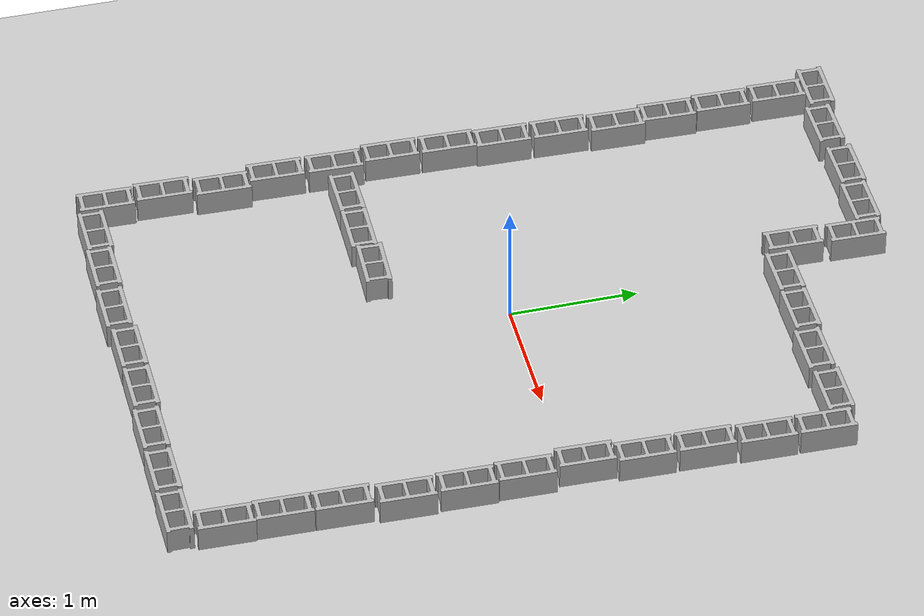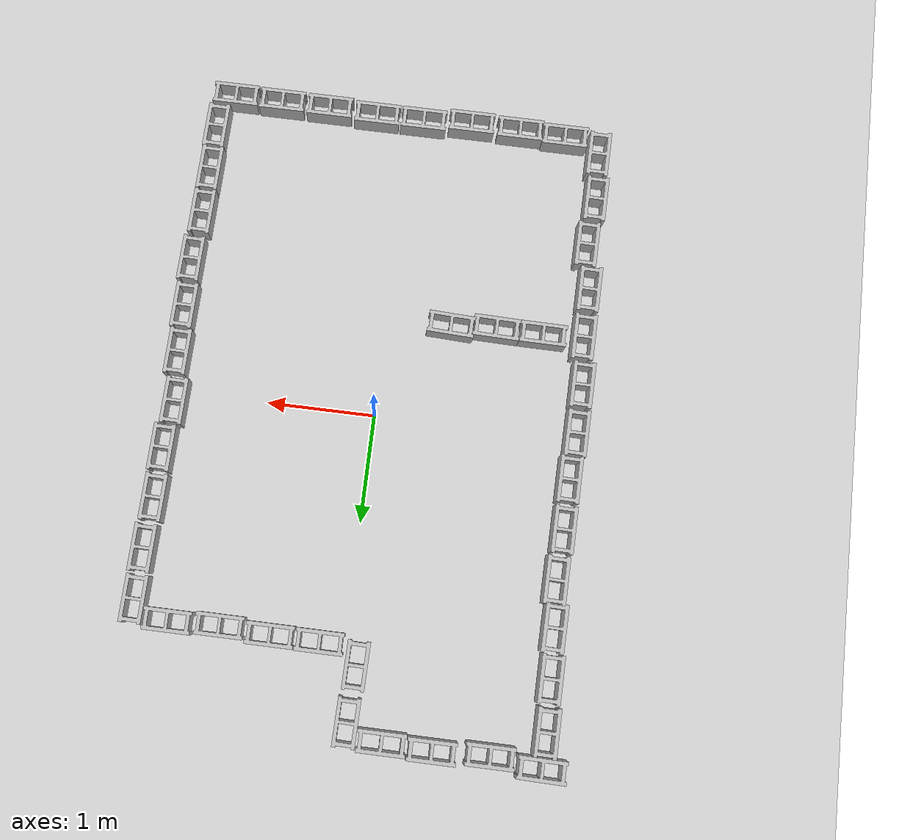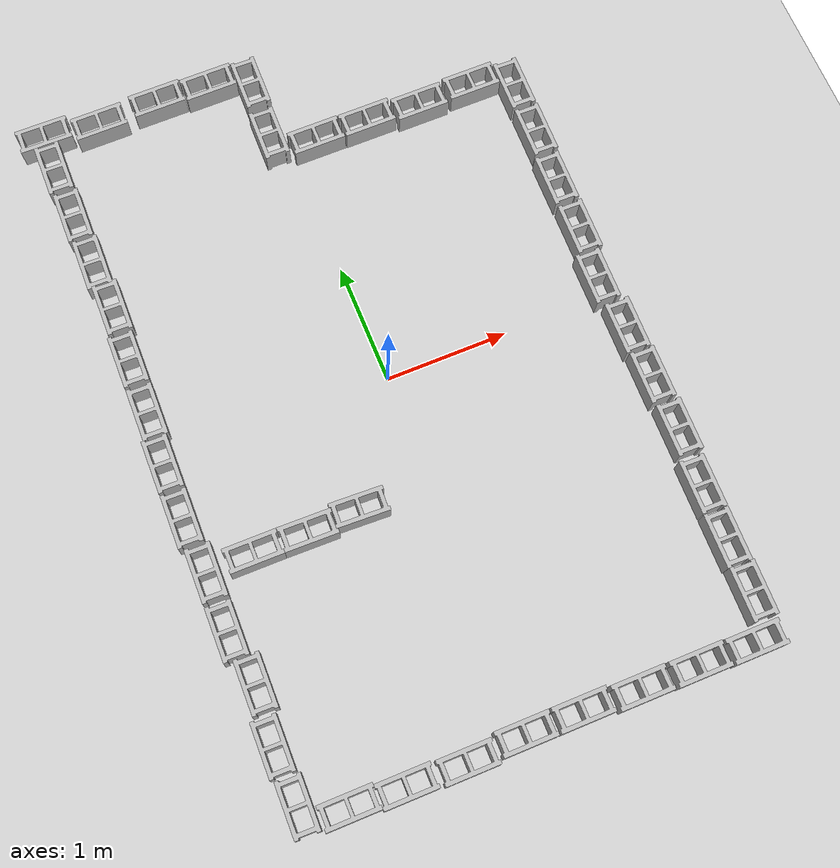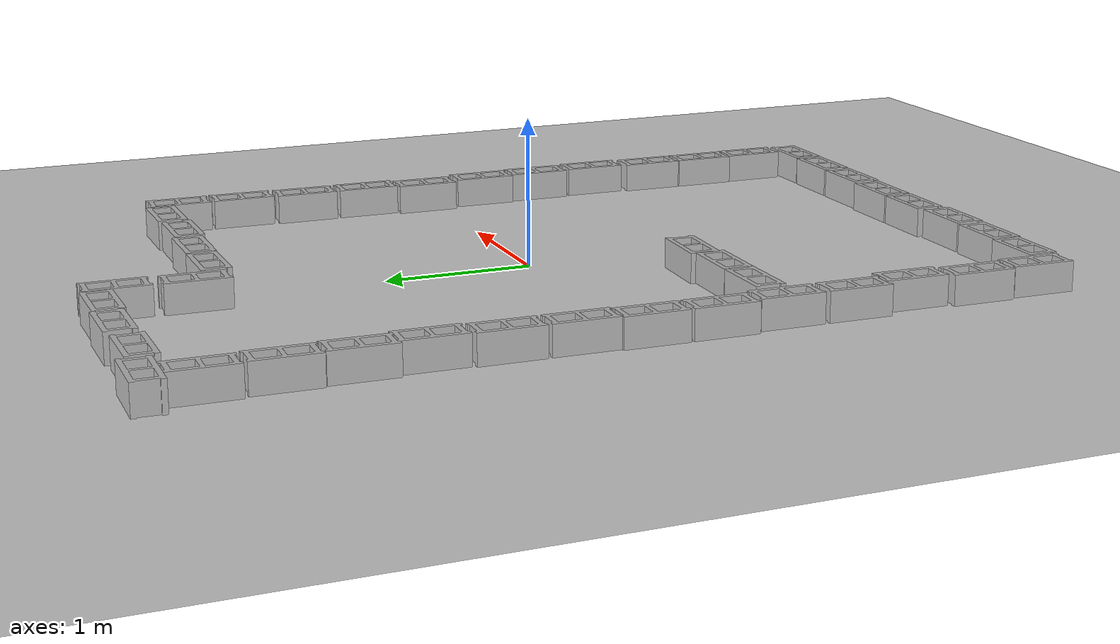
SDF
<sdf version="1.6">
 <world name="default">
  <light name="sun" type="directional">
   <pose>0 0 10 0 -0 0</pose>
   <diffuse>0.8 0.8 0.8 1</diffuse>
   <specular>0.2 0.2 0.2 1</specular>
   <attenuation>
    <range>1000</range>
    <constant>0.9</constant>
    <linear>0.01</linear>
    <quadratic>0.001</quadratic>
   </attenuation>
   <direction>-0.5 0.1 -0.9</direction>
  </light>
  <model name="ground_plane">
   <static>1</static>
   <link name="link">
    <collision name="collision">
     <geometry><plane><normal>0 0 1</normal><size>100 100</size></plane></geometry>
     <surface>
      <contact><collide_bitmask>65535</collide_bitmask></contact>
      <friction><ode><mu>100</mu><mu2>50</mu2></ode></friction>
     </surface>
    </collision>
    <visual name="visual">
     <cast_shadows>0</cast_shadows>
     <geometry><plane><normal>0 0 1</normal><size>100 100</size></plane></geometry>
     <material>
      <script><uri>file://media/materials/scripts/gazebo.material</uri><name>Gazebo/Grey</name></script>
     </material>
    </visual>
   </link>
  </model>
  <gravity>0 0 -9.8</gravity>
  <magnetic_field>6e-06 2.3e-05 -4.2e-05</magnetic_field>
  <atmosphere type="adiabatic"/>
  <physics name="default_physics" default="0" type="ode">
   <max_step_size>0.001</max_step_size>
   <real_time_factor>1</real_time_factor>
   <real_time_update_rate>1000</real_time_update_rate>
  </physics>
  <scene><ambient>0.4 0.4 0.4 1</ambient><background>0.7 0.7 0.7 1</background><shadows>1</shadows></scene>
  <audio><device>default</device></audio>
  <spherical_coordinates>
   <surface_model>EARTH_WGS84</surface_model>
   <latitude_deg>0</latitude_deg>
   <longitude_deg>0</longitude_deg>
   <elevation>0</elevation>
   <heading_deg>0</heading_deg>
  </spherical_coordinates>
  <model name="cinder_block">
   <link name="link">
    <inertial>
     <pose>0 0 0.1016 0 -0 0</pose>
     <mass>5</mass>
     <inertia>
      <ixx>0.028705</ixx>
      <ixy>0</ixy>
      <iyy>0.073708</iyy>
      <ixz>0</ixz>
      <iyz>0</iyz>
      <izz>0.06908</izz>
     </inertia>
    </inertial>
    <visual name="visual">
     <geometry><mesh><uri>model://cinder_block/meshes/cinder_block.dae</uri></mesh></geometry>
    </visual>
    <collision name="left">
     <pose>0 -0.08465 0.1016 0 -0 0</pose>
     <geometry><box><size>0.43495 0.0339 0.2032</size></box></geometry>
     <surface>
      <contact><ode><max_vel>0.1</max_vel><min_depth>0.001</min_depth></ode></contact>
      <friction><ode><mu>1</mu><mu2>1</mu2></ode></friction>
     </surface>
    </collision>
    <collision name="right">
     <pose>0 0.08465 0.1016 0 -0 0</pose>
     <geometry><box><size>0.43495 0.0339 0.2032</size></box></geometry>
     <surface>
      <contact><ode><max_vel>0.1</max_vel><min_depth>0.001</min_depth></ode></contact>
      <friction><ode><mu>1</mu><mu2>1</mu2></ode></friction>
     </surface>
    </collision>
    <collision name="front">
     <pose>0.18625 0 0.1016 0 -0 0</pose>
     <geometry><box><size>0.0339 0.1354 0.203</size></box></geometry>
     <surface>
      <contact><ode><max_vel>0.1</max_vel><min_depth>0.001</min_depth></ode></contact>
      <friction><ode><mu>1</mu><mu2>1</mu2></ode></friction>
     </surface>
    </collision>
    <collision name="middle">
     <pose>0 0 0.1016 0 -0 0</pose>
     <geometry><box><size>0.0339 0.1354 0.203</size></box></geometry>
     <surface>
      <contact><ode><max_vel>0.1</max_vel><min_depth>0.001</min_depth></ode></contact>
      <friction><ode><mu>1</mu><mu2>1</mu2></ode></friction>
     </surface>
    </collision>
    <collision name="back">
     <pose>-0.18625 0 0.1016 0 -0 0</pose>
     <geometry><box><size>0.0339 0.1354 0.203</size></box></geometry>
     <surface>
      <contact><ode><max_vel>0.1</max_vel><min_depth>0.001</min_depth></ode></contact>
      <friction><ode><mu>1</mu><mu2>1</mu2></ode></friction>
     </surface>
    </collision>
   </link>
   <pose>0.224611 2.1058 -6e-06 -1e-06 2.9e-05 0</pose>
  </model>
  <model name="cinder_block_0">
   <link name="link">
    <inertial>
     <pose>0 0 0.1016 0 -0 0</pose>
     <mass>5</mass>
     <inertia>
      <ixx>0.028705</ixx>
      <ixy>0</ixy>
      <iyy>0.073708</iyy>
      <ixz>0</ixz>
      <iyz>0</iyz>
      <izz>0.06908</izz>
     </inertia>
    </inertial>
    <visual name="visual">
     <geometry><mesh><uri>model://cinder_block/meshes/cinder_block.dae</uri></mesh></geometry>
    </visual>
    <collision name="left">
     <pose>0 -0.08465 0.1016 0 -0 0</pose>
     <geometry><box><size>0.43495 0.0339 0.2032</size></box></geometry>
     <surface>
      <contact><ode><max_vel>0.1</max_vel><min_depth>0.001</min_depth></ode></contact>
      <friction><ode><mu>1</mu><mu2>1</mu2></ode></friction>
     </surface>
    </collision>
    <collision name="right">
     <pose>0 0.08465 0.1016 0 -0 0</pose>
     <geometry><box><size>0.43495 0.0339 0.2032</size></box></geometry>
     <surface>
      <contact><ode><max_vel>0.1</max_vel><min_depth>0.001</min_depth></ode></contact>
      <friction><ode><mu>1</mu><mu2>1</mu2></ode></friction>
     </surface>
    </collision>
    <collision name="front">
     <pose>0.18625 0 0.1016 0 -0 0</pose>
     <geometry><box><size>0.0339 0.1354 0.203</size></box></geometry>
     <surface>
      <contact><ode><max_vel>0.1</max_vel><min_depth>0.001</min_depth></ode></contact>
      <friction><ode><mu>1</mu><mu2>1</mu2></ode></friction>
     </surface>
    </collision>
    <collision name="middle">
     <pose>0 0 0.1016 0 -0 0</pose>
     <geometry><box><size>0.0339 0.1354 0.203</size></box></geometry>
     <surface>
      <contact><ode><max_vel>0.1</max_vel><min_depth>0.001</min_depth></ode></contact>
      <friction><ode><mu>1</mu><mu2>1</mu2></ode></friction>
     </surface>
    </collision>
    <collision name="back">
     <pose>-0.18625 0 0.1016 0 -0 0</pose>
     <geometry><box><size>0.0339 0.1354 0.203</size></box></geometry>
     <surface>
      <contact><ode><max_vel>0.1</max_vel><min_depth>0.001</min_depth></ode></contact>
      <friction><ode><mu>1</mu><mu2>1</mu2></ode></friction>
     </surface>
    </collision>
   </link>
   <pose>0.669416 2.10145 -6e-06 -1e-06 2.9e-05 0</pose>
  </model>
  <model name="cinder_block_1">
   <link name="link">
    <inertial>
     <pose>0 0 0.1016 0 -0 0</pose>
     <mass>5</mass>
     <inertia>
      <ixx>0.028705</ixx>
      <ixy>0</ixy>
      <iyy>0.073708</iyy>
      <ixz>0</ixz>
      <iyz>0</iyz>
      <izz>0.06908</izz>
     </inertia>
    </inertial>
    <visual name="visual">
     <geometry><mesh><uri>model://cinder_block/meshes/cinder_block.dae</uri></mesh></geometry>
    </visual>
    <collision name="left">
     <pose>0 -0.08465 0.1016 0 -0 0</pose>
     <geometry><box><size>0.43495 0.0339 0.2032</size></box></geometry>
     <surface>
      <contact><ode><max_vel>0.1</max_vel><min_depth>0.001</min_depth></ode></contact>
      <friction><ode><mu>1</mu><mu2>1</mu2></ode></friction>
     </surface>
    </collision>
    <collision name="right">
     <pose>0 0.08465 0.1016 0 -0 0</pose>
     <geometry><box><size>0.43495 0.0339 0.2032</size></box></geometry>
     <surface>
      <contact><ode><max_vel>0.1</max_vel><min_depth>0.001</min_depth></ode></contact>
      <friction><ode><mu>1</mu><mu2>1</mu2></ode></friction>
     </surface>
    </collision>
    <collision name="front">
     <pose>0.18625 0 0.1016 0 -0 0</pose>
     <geometry><box><size>0.0339 0.1354 0.203</size></box></geometry>
     <surface>
      <contact><ode><max_vel>0.1</max_vel><min_depth>0.001</min_depth></ode></contact>
      <friction><ode><mu>1</mu><mu2>1</mu2></ode></friction>
     </surface>
    </collision>
    <collision name="middle">
     <pose>0 0 0.1016 0 -0 0</pose>
     <geometry><box><size>0.0339 0.1354 0.203</size></box></geometry>
     <surface>
      <contact><ode><max_vel>0.1</max_vel><min_depth>0.001</min_depth></ode></contact>
      <friction><ode><mu>1</mu><mu2>1</mu2></ode></friction>
     </surface>
    </collision>
    <collision name="back">
     <pose>-0.18625 0 0.1016 0 -0 0</pose>
     <geometry><box><size>0.0339 0.1354 0.203</size></box></geometry>
     <surface>
      <contact><ode><max_vel>0.1</max_vel><min_depth>0.001</min_depth></ode></contact>
      <friction><ode><mu>1</mu><mu2>1</mu2></ode></friction>
     </surface>
    </collision>
   </link>
   <pose>1.12399 2.07563 -6e-06 -1e-06 2.9e-05 0</pose>
  </model>
  <model name="cinder_block_2">
   <link name="link">
    <inertial>
     <pose>0 0 0.1016 0 -0 0</pose>
     <mass>5</mass>
     <inertia>
      <ixx>0.028705</ixx>
      <ixy>0</ixy>
      <iyy>0.073708</iyy>
      <ixz>0</ixz>
      <iyz>0</iyz>
      <izz>0.06908</izz>
     </inertia>
    </inertial>
    <visual name="visual">
     <geometry><mesh><uri>model://cinder_block/meshes/cinder_block.dae</uri></mesh></geometry>
    </visual>
    <collision name="left">
     <pose>0 -0.08465 0.1016 0 -0 0</pose>
     <geometry><box><size>0.43495 0.0339 0.2032</size></box></geometry>
     <surface>
      <contact><ode><max_vel>0.1</max_vel><min_depth>0.001</min_depth></ode></contact>
      <friction><ode><mu>1</mu><mu2>1</mu2></ode></friction>
     </surface>
    </collision>
    <collision name="right">
     <pose>0 0.08465 0.1016 0 -0 0</pose>
     <geometry><box><size>0.43495 0.0339 0.2032</size></box></geometry>
     <surface>
      <contact><ode><max_vel>0.1</max_vel><min_depth>0.001</min_depth></ode></contact>
      <friction><ode><mu>1</mu><mu2>1</mu2></ode></friction>
     </surface>
    </collision>
    <collision name="front">
     <pose>0.18625 0 0.1016 0 -0 0</pose>
     <geometry><box><size>0.0339 0.1354 0.203</size></box></geometry>
     <surface>
      <contact><ode><max_vel>0.1</max_vel><min_depth>0.001</min_depth></ode></contact>
      <friction><ode><mu>1</mu><mu2>1</mu2></ode></friction>
     </surface>
    </collision>
    <collision name="middle">
     <pose>0 0 0.1016 0 -0 0</pose>
     <geometry><box><size>0.0339 0.1354 0.203</size></box></geometry>
     <surface>
      <contact><ode><max_vel>0.1</max_vel><min_depth>0.001</min_depth></ode></contact>
      <friction><ode><mu>1</mu><mu2>1</mu2></ode></friction>
     </surface>
    </collision>
    <collision name="back">
     <pose>-0.18625 0 0.1016 0 -0 0</pose>
     <geometry><box><size>0.0339 0.1354 0.203</size></box></geometry>
     <surface>
      <contact><ode><max_vel>0.1</max_vel><min_depth>0.001</min_depth></ode></contact>
      <friction><ode><mu>1</mu><mu2>1</mu2></ode></friction>
     </surface>
    </collision>
   </link>
   <pose>1.59289 2.09049 -6e-06 -1e-06 2.9e-05 0</pose>
  </model>
  <model name="cinder_block_2_clone">
   <link name="link">
    <inertial>
     <pose>0 0 0.1016 0 -0 0</pose>
     <mass>5</mass>
     <inertia>
      <ixx>0.028705</ixx>
      <ixy>0</ixy>
      <iyy>0.073708</iyy>
      <ixz>0</ixz>
      <iyz>0</iyz>
      <izz>0.06908</izz>
     </inertia>
    </inertial>
    <visual name="visual">
     <geometry><mesh><uri>model://cinder_block/meshes/cinder_block.dae</uri></mesh></geometry>
    </visual>
    <collision name="left">
     <pose>0 -0.08465 0.1016 0 -0 0</pose>
     <geometry><box><size>0.43495 0.0339 0.2032</size></box></geometry>
     <surface>
      <contact><ode><max_vel>0.1</max_vel><min_depth>0.001</min_depth></ode></contact>
      <friction><ode><mu>1</mu><mu2>1</mu2></ode></friction>
     </surface>
    </collision>
    <collision name="right">
     <pose>0 0.08465 0.1016 0 -0 0</pose>
     <geometry><box><size>0.43495 0.0339 0.2032</size></box></geometry>
     <surface>
      <contact><ode><max_vel>0.1</max_vel><min_depth>0.001</min_depth></ode></contact>
      <friction><ode><mu>1</mu><mu2>1</mu2></ode></friction>
     </surface>
    </collision>
    <collision name="front">
     <pose>0.18625 0 0.1016 0 -0 0</pose>
     <geometry><box><size>0.0339 0.1354 0.203</size></box></geometry>
     <surface>
      <contact><ode><max_vel>0.1</max_vel><min_depth>0.001</min_depth></ode></contact>
      <friction><ode><mu>1</mu><mu2>1</mu2></ode></friction>
     </surface>
    </collision>
    <collision name="middle">
     <pose>0 0 0.1016 0 -0 0</pose>
     <geometry><box><size>0.0339 0.1354 0.203</size></box></geometry>
     <surface>
      <contact><ode><max_vel>0.1</max_vel><min_depth>0.001</min_depth></ode></contact>
      <friction><ode><mu>1</mu><mu2>1</mu2></ode></friction>
     </surface>
    </collision>
    <collision name="back">
     <pose>-0.18625 0 0.1016 0 -0 0</pose>
     <geometry><box><size>0.0339 0.1354 0.203</size></box></geometry>
     <surface>
      <contact><ode><max_vel>0.1</max_vel><min_depth>0.001</min_depth></ode></contact>
      <friction><ode><mu>1</mu><mu2>1</mu2></ode></friction>
     </surface>
    </collision>
   </link>
   <pose>1.91534 1.93639 -1.2e-05 6e-06 -0 -1.59062</pose>
  </model>
  <model name="cinder_block_2_clone_clone">
   <link name="link">
    <inertial>
     <pose>0 0 0.1016 0 -0 0</pose>
     <mass>5</mass>
     <inertia>
      <ixx>0.028705</ixx>
      <ixy>0</ixy>
      <iyy>0.073708</iyy>
      <ixz>0</ixz>
      <iyz>0</iyz>
      <izz>0.06908</izz>
     </inertia>
    </inertial>
    <visual name="visual">
     <geometry><mesh><uri>model://cinder_block/meshes/cinder_block.dae</uri></mesh></geometry>
    </visual>
    <collision name="left">
     <pose>0 -0.08465 0.1016 0 -0 0</pose>
     <geometry><box><size>0.43495 0.0339 0.2032</size></box></geometry>
     <surface>
      <contact><ode><max_vel>0.1</max_vel><min_depth>0.001</min_depth></ode></contact>
      <friction><ode><mu>1</mu><mu2>1</mu2></ode></friction>
     </surface>
    </collision>
    <collision name="right">
     <pose>0 0.08465 0.1016 0 -0 0</pose>
     <geometry><box><size>0.43495 0.0339 0.2032</size></box></geometry>
     <surface>
      <contact><ode><max_vel>0.1</max_vel><min_depth>0.001</min_depth></ode></contact>
      <friction><ode><mu>1</mu><mu2>1</mu2></ode></friction>
     </surface>
    </collision>
    <collision name="front">
     <pose>0.18625 0 0.1016 0 -0 0</pose>
     <geometry><box><size>0.0339 0.1354 0.203</size></box></geometry>
     <surface>
      <contact><ode><max_vel>0.1</max_vel><min_depth>0.001</min_depth></ode></contact>
      <friction><ode><mu>1</mu><mu2>1</mu2></ode></friction>
     </surface>
    </collision>
    <collision name="middle">
     <pose>0 0 0.1016 0 -0 0</pose>
     <geometry><box><size>0.0339 0.1354 0.203</size></box></geometry>
     <surface>
      <contact><ode><max_vel>0.1</max_vel><min_depth>0.001</min_depth></ode></contact>
      <friction><ode><mu>1</mu><mu2>1</mu2></ode></friction>
     </surface>
    </collision>
    <collision name="back">
     <pose>-0.18625 0 0.1016 0 -0 0</pose>
     <geometry><box><size>0.0339 0.1354 0.203</size></box></geometry>
     <surface>
      <contact><ode><max_vel>0.1</max_vel><min_depth>0.001</min_depth></ode></contact>
      <friction><ode><mu>1</mu><mu2>1</mu2></ode></friction>
     </surface>
    </collision>
   </link>
   <pose>1.91173 1.47972 -1.2e-05 6e-06 -0 -1.59062</pose>
  </model>
  <model name="cinder_block_2_clone_clone_0">
   <link name="link">
    <inertial>
     <pose>0 0 0.1016 0 -0 0</pose>
     <mass>5</mass>
     <inertia>
      <ixx>0.028705</ixx>
      <ixy>0</ixy>
      <iyy>0.073708</iyy>
      <ixz>0</ixz>
      <iyz>0</iyz>
      <izz>0.06908</izz>
     </inertia>
    </inertial>
    <visual name="visual">
     <geometry><mesh><uri>model://cinder_block/meshes/cinder_block.dae</uri></mesh></geometry>
    </visual>
    <collision name="left">
     <pose>0 -0.08465 0.1016 0 -0 0</pose>
     <geometry><box><size>0.43495 0.0339 0.2032</size></box></geometry>
     <surface>
      <contact><ode><max_vel>0.1</max_vel><min_depth>0.001</min_depth></ode></contact>
      <friction><ode><mu>1</mu><mu2>1</mu2></ode></friction>
     </surface>
    </collision>
    <collision name="right">
     <pose>0 0.08465 0.1016 0 -0 0</pose>
     <geometry><box><size>0.43495 0.0339 0.2032</size></box></geometry>
     <surface>
      <contact><ode><max_vel>0.1</max_vel><min_depth>0.001</min_depth></ode></contact>
      <friction><ode><mu>1</mu><mu2>1</mu2></ode></friction>
     </surface>
    </collision>
    <collision name="front">
     <pose>0.18625 0 0.1016 0 -0 0</pose>
     <geometry><box><size>0.0339 0.1354 0.203</size></box></geometry>
     <surface>
      <contact><ode><max_vel>0.1</max_vel><min_depth>0.001</min_depth></ode></contact>
      <friction><ode><mu>1</mu><mu2>1</mu2></ode></friction>
     </surface>
    </collision>
    <collision name="middle">
     <pose>0 0 0.1016 0 -0 0</pose>
     <geometry><box><size>0.0339 0.1354 0.203</size></box></geometry>
     <surface>
      <contact><ode><max_vel>0.1</max_vel><min_depth>0.001</min_depth></ode></contact>
      <friction><ode><mu>1</mu><mu2>1</mu2></ode></friction>
     </surface>
    </collision>
    <collision name="back">
     <pose>-0.18625 0 0.1016 0 -0 0</pose>
     <geometry><box><size>0.0339 0.1354 0.203</size></box></geometry>
     <surface>
      <contact><ode><max_vel>0.1</max_vel><min_depth>0.001</min_depth></ode></contact>
      <friction><ode><mu>1</mu><mu2>1</mu2></ode></friction>
     </surface>
    </collision>
   </link>
   <pose>1.8877 1.01666 -1.2e-05 5e-06 0 -1.59062</pose>
  </model>
  <model name="cinder_block_2_clone_clone_1">
   <link name="link">
    <inertial>
     <pose>0 0 0.1016 0 -0 0</pose>
     <mass>5</mass>
     <inertia>
      <ixx>0.028705</ixx>
      <ixy>0</ixy>
      <iyy>0.073708</iyy>
      <ixz>0</ixz>
      <iyz>0</iyz>
      <izz>0.06908</izz>
     </inertia>
    </inertial>
    <visual name="visual">
     <geometry><mesh><uri>model://cinder_block/meshes/cinder_block.dae</uri></mesh></geometry>
    </visual>
    <collision name="left">
     <pose>0 -0.08465 0.1016 0 -0 0</pose>
     <geometry><box><size>0.43495 0.0339 0.2032</size></box></geometry>
     <surface>
      <contact><ode><max_vel>0.1</max_vel><min_depth>0.001</min_depth></ode></contact>
      <friction><ode><mu>1</mu><mu2>1</mu2></ode></friction>
     </surface>
    </collision>
    <collision name="right">
     <pose>0 0.08465 0.1016 0 -0 0</pose>
     <geometry><box><size>0.43495 0.0339 0.2032</size></box></geometry>
     <surface>
      <contact><ode><max_vel>0.1</max_vel><min_depth>0.001</min_depth></ode></contact>
      <friction><ode><mu>1</mu><mu2>1</mu2></ode></friction>
     </surface>
    </collision>
    <collision name="front">
     <pose>0.18625 0 0.1016 0 -0 0</pose>
     <geometry><box><size>0.0339 0.1354 0.203</size></box></geometry>
     <surface>
      <contact><ode><max_vel>0.1</max_vel><min_depth>0.001</min_depth></ode></contact>
      <friction><ode><mu>1</mu><mu2>1</mu2></ode></friction>
     </surface>
    </collision>
    <collision name="middle">
     <pose>0 0 0.1016 0 -0 0</pose>
     <geometry><box><size>0.0339 0.1354 0.203</size></box></geometry>
     <surface>
      <contact><ode><max_vel>0.1</max_vel><min_depth>0.001</min_depth></ode></contact>
      <friction><ode><mu>1</mu><mu2>1</mu2></ode></friction>
     </surface>
    </collision>
    <collision name="back">
     <pose>-0.18625 0 0.1016 0 -0 0</pose>
     <geometry><box><size>0.0339 0.1354 0.203</size></box></geometry>
     <surface>
      <contact><ode><max_vel>0.1</max_vel><min_depth>0.001</min_depth></ode></contact>
      <friction><ode><mu>1</mu><mu2>1</mu2></ode></friction>
     </surface>
    </collision>
   </link>
   <pose>1.88472 0.556425 -1.2e-05 5e-06 0 -1.59062</pose>
  </model>
  <model name="cinder_block_2_clone_clone_2">
   <link name="link">
    <inertial>
     <pose>0 0 0.1016 0 -0 0</pose>
     <mass>5</mass>
     <inertia>
      <ixx>0.028705</ixx>
      <ixy>0</ixy>
      <iyy>0.073708</iyy>
      <ixz>0</ixz>
      <iyz>0</iyz>
      <izz>0.06908</izz>
     </inertia>
    </inertial>
    <visual name="visual">
     <geometry><mesh><uri>model://cinder_block/meshes/cinder_block.dae</uri></mesh></geometry>
    </visual>
    <collision name="left">
     <pose>0 -0.08465 0.1016 0 -0 0</pose>
     <geometry><box><size>0.43495 0.0339 0.2032</size></box></geometry>
     <surface>
      <contact><ode><max_vel>0.1</max_vel><min_depth>0.001</min_depth></ode></contact>
      <friction><ode><mu>1</mu><mu2>1</mu2></ode></friction>
     </surface>
    </collision>
    <collision name="right">
     <pose>0 0.08465 0.1016 0 -0 0</pose>
     <geometry><box><size>0.43495 0.0339 0.2032</size></box></geometry>
     <surface>
      <contact><ode><max_vel>0.1</max_vel><min_depth>0.001</min_depth></ode></contact>
      <friction><ode><mu>1</mu><mu2>1</mu2></ode></friction>
     </surface>
    </collision>
    <collision name="front">
     <pose>0.18625 0 0.1016 0 -0 0</pose>
     <geometry><box><size>0.0339 0.1354 0.203</size></box></geometry>
     <surface>
      <contact><ode><max_vel>0.1</max_vel><min_depth>0.001</min_depth></ode></contact>
      <friction><ode><mu>1</mu><mu2>1</mu2></ode></friction>
     </surface>
    </collision>
    <collision name="middle">
     <pose>0 0 0.1016 0 -0 0</pose>
     <geometry><box><size>0.0339 0.1354 0.203</size></box></geometry>
     <surface>
      <contact><ode><max_vel>0.1</max_vel><min_depth>0.001</min_depth></ode></contact>
      <friction><ode><mu>1</mu><mu2>1</mu2></ode></friction>
     </surface>
    </collision>
    <collision name="back">
     <pose>-0.18625 0 0.1016 0 -0 0</pose>
     <geometry><box><size>0.0339 0.1354 0.203</size></box></geometry>
     <surface>
      <contact><ode><max_vel>0.1</max_vel><min_depth>0.001</min_depth></ode></contact>
      <friction><ode><mu>1</mu><mu2>1</mu2></ode></friction>
     </surface>
    </collision>
   </link>
   <pose>1.83849 0.113223 -1.2e-05 5e-06 0 -1.59062</pose>
  </model>
  <model name="cinder_block_2_clone_clone_3">
   <link name="link">
    <inertial>
     <pose>0 0 0.1016 0 -0 0</pose>
     <mass>5</mass>
     <inertia>
      <ixx>0.028705</ixx>
      <ixy>0</ixy>
      <iyy>0.073708</iyy>
      <ixz>0</ixz>
      <iyz>0</iyz>
      <izz>0.06908</izz>
     </inertia>
    </inertial>
    <visual name="visual">
     <geometry><mesh><uri>model://cinder_block/meshes/cinder_block.dae</uri></mesh></geometry>
    </visual>
    <collision name="left">
     <pose>0 -0.08465 0.1016 0 -0 0</pose>
     <geometry><box><size>0.43495 0.0339 0.2032</size></box></geometry>
     <surface>
      <contact><ode><max_vel>0.1</max_vel><min_depth>0.001</min_depth></ode></contact>
      <friction><ode><mu>1</mu><mu2>1</mu2></ode></friction>
     </surface>
    </collision>
    <collision name="right">
     <pose>0 0.08465 0.1016 0 -0 0</pose>
     <geometry><box><size>0.43495 0.0339 0.2032</size></box></geometry>
     <surface>
      <contact><ode><max_vel>0.1</max_vel><min_depth>0.001</min_depth></ode></contact>
      <friction><ode><mu>1</mu><mu2>1</mu2></ode></friction>
     </surface>
    </collision>
    <collision name="front">
     <pose>0.18625 0 0.1016 0 -0 0</pose>
     <geometry><box><size>0.0339 0.1354 0.203</size></box></geometry>
     <surface>
      <contact><ode><max_vel>0.1</max_vel><min_depth>0.001</min_depth></ode></contact>
      <friction><ode><mu>1</mu><mu2>1</mu2></ode></friction>
     </surface>
    </collision>
    <collision name="middle">
     <pose>0 0 0.1016 0 -0 0</pose>
     <geometry><box><size>0.0339 0.1354 0.203</size></box></geometry>
     <surface>
      <contact><ode><max_vel>0.1</max_vel><min_depth>0.001</min_depth></ode></contact>
      <friction><ode><mu>1</mu><mu2>1</mu2></ode></friction>
     </surface>
    </collision>
    <collision name="back">
     <pose>-0.18625 0 0.1016 0 -0 0</pose>
     <geometry><box><size>0.0339 0.1354 0.203</size></box></geometry>
     <surface>
      <contact><ode><max_vel>0.1</max_vel><min_depth>0.001</min_depth></ode></contact>
      <friction><ode><mu>1</mu><mu2>1</mu2></ode></friction>
     </surface>
    </collision>
   </link>
   <pose>1.87798 -0.351042 -1.2e-05 5e-06 0 -1.59062</pose>
  </model>
  <model name="cinder_block_2_clone_clone_4">
   <link name="link">
    <inertial>
     <pose>0 0 0.1016 0 -0 0</pose>
     <mass>5</mass>
     <inertia>
      <ixx>0.028705</ixx>
      <ixy>0</ixy>
      <iyy>0.073708</iyy>
      <ixz>0</ixz>
      <iyz>0</iyz>
      <izz>0.06908</izz>
     </inertia>
    </inertial>
    <visual name="visual">
     <geometry><mesh><uri>model://cinder_block/meshes/cinder_block.dae</uri></mesh></geometry>
    </visual>
    <collision name="left">
     <pose>0 -0.08465 0.1016 0 -0 0</pose>
     <geometry><box><size>0.43495 0.0339 0.2032</size></box></geometry>
     <surface>
      <contact><ode><max_vel>0.1</max_vel><min_depth>0.001</min_depth></ode></contact>
      <friction><ode><mu>1</mu><mu2>1</mu2></ode></friction>
     </surface>
    </collision>
    <collision name="right">
     <pose>0 0.08465 0.1016 0 -0 0</pose>
     <geometry><box><size>0.43495 0.0339 0.2032</size></box></geometry>
     <surface>
      <contact><ode><max_vel>0.1</max_vel><min_depth>0.001</min_depth></ode></contact>
      <friction><ode><mu>1</mu><mu2>1</mu2></ode></friction>
     </surface>
    </collision>
    <collision name="front">
     <pose>0.18625 0 0.1016 0 -0 0</pose>
     <geometry><box><size>0.0339 0.1354 0.203</size></box></geometry>
     <surface>
      <contact><ode><max_vel>0.1</max_vel><min_depth>0.001</min_depth></ode></contact>
      <friction><ode><mu>1</mu><mu2>1</mu2></ode></friction>
     </surface>
    </collision>
    <collision name="middle">
     <pose>0 0 0.1016 0 -0 0</pose>
     <geometry><box><size>0.0339 0.1354 0.203</size></box></geometry>
     <surface>
      <contact><ode><max_vel>0.1</max_vel><min_depth>0.001</min_depth></ode></contact>
      <friction><ode><mu>1</mu><mu2>1</mu2></ode></friction>
     </surface>
    </collision>
    <collision name="back">
     <pose>-0.18625 0 0.1016 0 -0 0</pose>
     <geometry><box><size>0.0339 0.1354 0.203</size></box></geometry>
     <surface>
      <contact><ode><max_vel>0.1</max_vel><min_depth>0.001</min_depth></ode></contact>
      <friction><ode><mu>1</mu><mu2>1</mu2></ode></friction>
     </surface>
    </collision>
   </link>
   <pose>1.88676 -0.795198 -1.2e-05 5e-06 0 -1.59062</pose>
  </model>
  <model name="cinder_block_2_clone_clone_5">
   <link name="link">
    <inertial>
     <pose>0 0 0.1016 0 -0 0</pose>
     <mass>5</mass>
     <inertia>
      <ixx>0.028705</ixx>
      <ixy>0</ixy>
      <iyy>0.073708</iyy>
      <ixz>0</ixz>
      <iyz>0</iyz>
      <izz>0.06908</izz>
     </inertia>
    </inertial>
    <visual name="visual">
     <geometry><mesh><uri>model://cinder_block/meshes/cinder_block.dae</uri></mesh></geometry>
    </visual>
    <collision name="left">
     <pose>0 -0.08465 0.1016 0 -0 0</pose>
     <geometry><box><size>0.43495 0.0339 0.2032</size></box></geometry>
     <surface>
      <contact><ode><max_vel>0.1</max_vel><min_depth>0.001</min_depth></ode></contact>
      <friction><ode><mu>1</mu><mu2>1</mu2></ode></friction>
     </surface>
    </collision>
    <collision name="right">
     <pose>0 0.08465 0.1016 0 -0 0</pose>
     <geometry><box><size>0.43495 0.0339 0.2032</size></box></geometry>
     <surface>
      <contact><ode><max_vel>0.1</max_vel><min_depth>0.001</min_depth></ode></contact>
      <friction><ode><mu>1</mu><mu2>1</mu2></ode></friction>
     </surface>
    </collision>
    <collision name="front">
     <pose>0.18625 0 0.1016 0 -0 0</pose>
     <geometry><box><size>0.0339 0.1354 0.203</size></box></geometry>
     <surface>
      <contact><ode><max_vel>0.1</max_vel><min_depth>0.001</min_depth></ode></contact>
      <friction><ode><mu>1</mu><mu2>1</mu2></ode></friction>
     </surface>
    </collision>
    <collision name="middle">
     <pose>0 0 0.1016 0 -0 0</pose>
     <geometry><box><size>0.0339 0.1354 0.203</size></box></geometry>
     <surface>
      <contact><ode><max_vel>0.1</max_vel><min_depth>0.001</min_depth></ode></contact>
      <friction><ode><mu>1</mu><mu2>1</mu2></ode></friction>
     </surface>
    </collision>
    <collision name="back">
     <pose>-0.18625 0 0.1016 0 -0 0</pose>
     <geometry><box><size>0.0339 0.1354 0.203</size></box></geometry>
     <surface>
      <contact><ode><max_vel>0.1</max_vel><min_depth>0.001</min_depth></ode></contact>
      <friction><ode><mu>1</mu><mu2>1</mu2></ode></friction>
     </surface>
    </collision>
   </link>
   <pose>1.89433 -1.2558 -1.2e-05 5e-06 0 -1.59062</pose>
  </model>
  <model name="cinder_block_2_clone_clone_6">
   <link name="link">
    <inertial>
     <pose>0 0 0.1016 0 -0 0</pose>
     <mass>5</mass>
     <inertia>
      <ixx>0.028705</ixx>
      <ixy>0</ixy>
      <iyy>0.073708</iyy>
      <ixz>0</ixz>
      <iyz>0</iyz>
      <izz>0.06908</izz>
     </inertia>
    </inertial>
    <visual name="visual">
     <geometry><mesh><uri>model://cinder_block/meshes/cinder_block.dae</uri></mesh></geometry>
    </visual>
    <collision name="left">
     <pose>0 -0.08465 0.1016 0 -0 0</pose>
     <geometry><box><size>0.43495 0.0339 0.2032</size></box></geometry>
     <surface>
      <contact><ode><max_vel>0.1</max_vel><min_depth>0.001</min_depth></ode></contact>
      <friction><ode><mu>1</mu><mu2>1</mu2></ode></friction>
     </surface>
    </collision>
    <collision name="right">
     <pose>0 0.08465 0.1016 0 -0 0</pose>
     <geometry><box><size>0.43495 0.0339 0.2032</size></box></geometry>
     <surface>
      <contact><ode><max_vel>0.1</max_vel><min_depth>0.001</min_depth></ode></contact>
      <friction><ode><mu>1</mu><mu2>1</mu2></ode></friction>
     </surface>
    </collision>
    <collision name="front">
     <pose>0.18625 0 0.1016 0 -0 0</pose>
     <geometry><box><size>0.0339 0.1354 0.203</size></box></geometry>
     <surface>
      <contact><ode><max_vel>0.1</max_vel><min_depth>0.001</min_depth></ode></contact>
      <friction><ode><mu>1</mu><mu2>1</mu2></ode></friction>
     </surface>
    </collision>
    <collision name="middle">
     <pose>0 0 0.1016 0 -0 0</pose>
     <geometry><box><size>0.0339 0.1354 0.203</size></box></geometry>
     <surface>
      <contact><ode><max_vel>0.1</max_vel><min_depth>0.001</min_depth></ode></contact>
      <friction><ode><mu>1</mu><mu2>1</mu2></ode></friction>
     </surface>
    </collision>
    <collision name="back">
     <pose>-0.18625 0 0.1016 0 -0 0</pose>
     <geometry><box><size>0.0339 0.1354 0.203</size></box></geometry>
     <surface>
      <contact><ode><max_vel>0.1</max_vel><min_depth>0.001</min_depth></ode></contact>
      <friction><ode><mu>1</mu><mu2>1</mu2></ode></friction>
     </surface>
    </collision>
   </link>
   <pose>1.86231 -1.72734 -1.2e-05 5e-06 0 -1.59062</pose>
  </model>
  <model name="cinder_block_2_clone_clone_7">
   <link name="link">
    <inertial>
     <pose>0 0 0.1016 0 -0 0</pose>
     <mass>5</mass>
     <inertia>
      <ixx>0.028705</ixx>
      <ixy>0</ixy>
      <iyy>0.073708</iyy>
      <ixz>0</ixz>
      <iyz>0</iyz>
      <izz>0.06908</izz>
     </inertia>
    </inertial>
    <visual name="visual">
     <geometry><mesh><uri>model://cinder_block/meshes/cinder_block.dae</uri></mesh></geometry>
    </visual>
    <collision name="left">
     <pose>0 -0.08465 0.1016 0 -0 0</pose>
     <geometry><box><size>0.43495 0.0339 0.2032</size></box></geometry>
     <surface>
      <contact><ode><max_vel>0.1</max_vel><min_depth>0.001</min_depth></ode></contact>
      <friction><ode><mu>1</mu><mu2>1</mu2></ode></friction>
     </surface>
    </collision>
    <collision name="right">
     <pose>0 0.08465 0.1016 0 -0 0</pose>
     <geometry><box><size>0.43495 0.0339 0.2032</size></box></geometry>
     <surface>
      <contact><ode><max_vel>0.1</max_vel><min_depth>0.001</min_depth></ode></contact>
      <friction><ode><mu>1</mu><mu2>1</mu2></ode></friction>
     </surface>
    </collision>
    <collision name="front">
     <pose>0.18625 0 0.1016 0 -0 0</pose>
     <geometry><box><size>0.0339 0.1354 0.203</size></box></geometry>
     <surface>
      <contact><ode><max_vel>0.1</max_vel><min_depth>0.001</min_depth></ode></contact>
      <friction><ode><mu>1</mu><mu2>1</mu2></ode></friction>
     </surface>
    </collision>
    <collision name="middle">
     <pose>0 0 0.1016 0 -0 0</pose>
     <geometry><box><size>0.0339 0.1354 0.203</size></box></geometry>
     <surface>
      <contact><ode><max_vel>0.1</max_vel><min_depth>0.001</min_depth></ode></contact>
      <friction><ode><mu>1</mu><mu2>1</mu2></ode></friction>
     </surface>
    </collision>
    <collision name="back">
     <pose>-0.18625 0 0.1016 0 -0 0</pose>
     <geometry><box><size>0.0339 0.1354 0.203</size></box></geometry>
     <surface>
      <contact><ode><max_vel>0.1</max_vel><min_depth>0.001</min_depth></ode></contact>
      <friction><ode><mu>1</mu><mu2>1</mu2></ode></friction>
     </surface>
    </collision>
   </link>
   <pose>1.85298 -2.16877 -1.2e-05 4e-06 -0 -1.59037</pose>
  </model>
  <model name="cinder_block_2_clone_clone_8">
   <link name="link">
    <inertial>
     <pose>0 0 0.1016 0 -0 0</pose>
     <mass>5</mass>
     <inertia>
      <ixx>0.028705</ixx>
      <ixy>0</ixy>
      <iyy>0.073708</iyy>
      <ixz>0</ixz>
      <iyz>0</iyz>
      <izz>0.06908</izz>
     </inertia>
    </inertial>
    <visual name="visual">
     <geometry><mesh><uri>model://cinder_block/meshes/cinder_block.dae</uri></mesh></geometry>
    </visual>
    <collision name="left">
     <pose>0 -0.08465 0.1016 0 -0 0</pose>
     <geometry><box><size>0.43495 0.0339 0.2032</size></box></geometry>
     <surface>
      <contact><ode><max_vel>0.1</max_vel><min_depth>0.001</min_depth></ode></contact>
      <friction><ode><mu>1</mu><mu2>1</mu2></ode></friction>
     </surface>
    </collision>
    <collision name="right">
     <pose>0 0.08465 0.1016 0 -0 0</pose>
     <geometry><box><size>0.43495 0.0339 0.2032</size></box></geometry>
     <surface>
      <contact><ode><max_vel>0.1</max_vel><min_depth>0.001</min_depth></ode></contact>
      <friction><ode><mu>1</mu><mu2>1</mu2></ode></friction>
     </surface>
    </collision>
    <collision name="front">
     <pose>0.18625 0 0.1016 0 -0 0</pose>
     <geometry><box><size>0.0339 0.1354 0.203</size></box></geometry>
     <surface>
      <contact><ode><max_vel>0.1</max_vel><min_depth>0.001</min_depth></ode></contact>
      <friction><ode><mu>1</mu><mu2>1</mu2></ode></friction>
     </surface>
    </collision>
    <collision name="middle">
     <pose>0 0 0.1016 0 -0 0</pose>
     <geometry><box><size>0.0339 0.1354 0.203</size></box></geometry>
     <surface>
      <contact><ode><max_vel>0.1</max_vel><min_depth>0.001</min_depth></ode></contact>
      <friction><ode><mu>1</mu><mu2>1</mu2></ode></friction>
     </surface>
    </collision>
    <collision name="back">
     <pose>-0.18625 0 0.1016 0 -0 0</pose>
     <geometry><box><size>0.0339 0.1354 0.203</size></box></geometry>
     <surface>
      <contact><ode><max_vel>0.1</max_vel><min_depth>0.001</min_depth></ode></contact>
      <friction><ode><mu>1</mu><mu2>1</mu2></ode></friction>
     </surface>
    </collision>
   </link>
   <pose>1.85442 -2.60304 -1.2e-05 4e-06 -0 -1.59037</pose>
  </model>
  <model name="cinder_block_1_clone">
   <link name="link">
    <inertial>
     <pose>0 0 0.1016 0 -0 0</pose>
     <mass>5</mass>
     <inertia>
      <ixx>0.028705</ixx>
      <ixy>0</ixy>
      <iyy>0.073708</iyy>
      <ixz>0</ixz>
      <iyz>0</iyz>
      <izz>0.06908</izz>
     </inertia>
    </inertial>
    <visual name="visual">
     <geometry><mesh><uri>model://cinder_block/meshes/cinder_block.dae</uri></mesh></geometry>
    </visual>
    <collision name="left">
     <pose>0 -0.08465 0.1016 0 -0 0</pose>
     <geometry><box><size>0.43495 0.0339 0.2032</size></box></geometry>
     <surface>
      <contact><ode><max_vel>0.1</max_vel><min_depth>0.001</min_depth></ode></contact>
      <friction><ode><mu>1</mu><mu2>1</mu2></ode></friction>
     </surface>
    </collision>
    <collision name="right">
     <pose>0 0.08465 0.1016 0 -0 0</pose>
     <geometry><box><size>0.43495 0.0339 0.2032</size></box></geometry>
     <surface>
      <contact><ode><max_vel>0.1</max_vel><min_depth>0.001</min_depth></ode></contact>
      <friction><ode><mu>1</mu><mu2>1</mu2></ode></friction>
     </surface>
    </collision>
    <collision name="front">
     <pose>0.18625 0 0.1016 0 -0 0</pose>
     <geometry><box><size>0.0339 0.1354 0.203</size></box></geometry>
     <surface>
      <contact><ode><max_vel>0.1</max_vel><min_depth>0.001</min_depth></ode></contact>
      <friction><ode><mu>1</mu><mu2>1</mu2></ode></friction>
     </surface>
    </collision>
    <collision name="middle">
     <pose>0 0 0.1016 0 -0 0</pose>
     <geometry><box><size>0.0339 0.1354 0.203</size></box></geometry>
     <surface>
      <contact><ode><max_vel>0.1</max_vel><min_depth>0.001</min_depth></ode></contact>
      <friction><ode><mu>1</mu><mu2>1</mu2></ode></friction>
     </surface>
    </collision>
    <collision name="back">
     <pose>-0.18625 0 0.1016 0 -0 0</pose>
     <geometry><box><size>0.0339 0.1354 0.203</size></box></geometry>
     <surface>
      <contact><ode><max_vel>0.1</max_vel><min_depth>0.001</min_depth></ode></contact>
      <friction><ode><mu>1</mu><mu2>1</mu2></ode></friction>
     </surface>
    </collision>
   </link>
   <pose>1.70955 -2.94654 -6e-06 5e-06 2.5e-05 0</pose>
  </model>
  <model name="cinder_block_1_clone_0">
   <link name="link">
    <inertial>
     <pose>0 0 0.1016 0 -0 0</pose>
     <mass>5</mass>
     <inertia>
      <ixx>0.028705</ixx>
      <ixy>0</ixy>
      <iyy>0.073708</iyy>
      <ixz>0</ixz>
      <iyz>0</iyz>
      <izz>0.06908</izz>
     </inertia>
    </inertial>
    <visual name="visual">
     <geometry><mesh><uri>model://cinder_block/meshes/cinder_block.dae</uri></mesh></geometry>
    </visual>
    <collision name="left">
     <pose>0 -0.08465 0.1016 0 -0 0</pose>
     <geometry><box><size>0.43495 0.0339 0.2032</size></box></geometry>
     <surface>
      <contact><ode><max_vel>0.1</max_vel><min_depth>0.001</min_depth></ode></contact>
      <friction><ode><mu>1</mu><mu2>1</mu2></ode></friction>
     </surface>
    </collision>
    <collision name="right">
     <pose>0 0.08465 0.1016 0 -0 0</pose>
     <geometry><box><size>0.43495 0.0339 0.2032</size></box></geometry>
     <surface>
      <contact><ode><max_vel>0.1</max_vel><min_depth>0.001</min_depth></ode></contact>
      <friction><ode><mu>1</mu><mu2>1</mu2></ode></friction>
     </surface>
    </collision>
    <collision name="front">
     <pose>0.18625 0 0.1016 0 -0 0</pose>
     <geometry><box><size>0.0339 0.1354 0.203</size></box></geometry>
     <surface>
      <contact><ode><max_vel>0.1</max_vel><min_depth>0.001</min_depth></ode></contact>
      <friction><ode><mu>1</mu><mu2>1</mu2></ode></friction>
     </surface>
    </collision>
    <collision name="middle">
     <pose>0 0 0.1016 0 -0 0</pose>
     <geometry><box><size>0.0339 0.1354 0.203</size></box></geometry>
     <surface>
      <contact><ode><max_vel>0.1</max_vel><min_depth>0.001</min_depth></ode></contact>
      <friction><ode><mu>1</mu><mu2>1</mu2></ode></friction>
     </surface>
    </collision>
    <collision name="back">
     <pose>-0.18625 0 0.1016 0 -0 0</pose>
     <geometry><box><size>0.0339 0.1354 0.203</size></box></geometry>
     <surface>
      <contact><ode><max_vel>0.1</max_vel><min_depth>0.001</min_depth></ode></contact>
      <friction><ode><mu>1</mu><mu2>1</mu2></ode></friction>
     </surface>
    </collision>
   </link>
   <pose>1.25685 -2.9397 -6e-06 5e-06 2.5e-05 0</pose>
  </model>
  <model name="cinder_block_1_clone_1">
   <link name="link">
    <inertial>
     <pose>0 0 0.1016 0 -0 0</pose>
     <mass>5</mass>
     <inertia>
      <ixx>0.028705</ixx>
      <ixy>0</ixy>
      <iyy>0.073708</iyy>
      <ixz>0</ixz>
      <iyz>0</iyz>
      <izz>0.06908</izz>
     </inertia>
    </inertial>
    <visual name="visual">
     <geometry><mesh><uri>model://cinder_block/meshes/cinder_block.dae</uri></mesh></geometry>
    </visual>
    <collision name="left">
     <pose>0 -0.08465 0.1016 0 -0 0</pose>
     <geometry><box><size>0.43495 0.0339 0.2032</size></box></geometry>
     <surface>
      <contact><ode><max_vel>0.1</max_vel><min_depth>0.001</min_depth></ode></contact>
      <friction><ode><mu>1</mu><mu2>1</mu2></ode></friction>
     </surface>
    </collision>
    <collision name="right">
     <pose>0 0.08465 0.1016 0 -0 0</pose>
     <geometry><box><size>0.43495 0.0339 0.2032</size></box></geometry>
     <surface>
      <contact><ode><max_vel>0.1</max_vel><min_depth>0.001</min_depth></ode></contact>
      <friction><ode><mu>1</mu><mu2>1</mu2></ode></friction>
     </surface>
    </collision>
    <collision name="front">
     <pose>0.18625 0 0.1016 0 -0 0</pose>
     <geometry><box><size>0.0339 0.1354 0.203</size></box></geometry>
     <surface>
      <contact><ode><max_vel>0.1</max_vel><min_depth>0.001</min_depth></ode></contact>
      <friction><ode><mu>1</mu><mu2>1</mu2></ode></friction>
     </surface>
    </collision>
    <collision name="middle">
     <pose>0 0 0.1016 0 -0 0</pose>
     <geometry><box><size>0.0339 0.1354 0.203</size></box></geometry>
     <surface>
      <contact><ode><max_vel>0.1</max_vel><min_depth>0.001</min_depth></ode></contact>
      <friction><ode><mu>1</mu><mu2>1</mu2></ode></friction>
     </surface>
    </collision>
    <collision name="back">
     <pose>-0.18625 0 0.1016 0 -0 0</pose>
     <geometry><box><size>0.0339 0.1354 0.203</size></box></geometry>
     <surface>
      <contact><ode><max_vel>0.1</max_vel><min_depth>0.001</min_depth></ode></contact>
      <friction><ode><mu>1</mu><mu2>1</mu2></ode></friction>
     </surface>
    </collision>
   </link>
   <pose>0.793336 -2.93487 -6e-06 5e-06 2.5e-05 0</pose>
  </model>
  <model name="cinder_block_1_clone_2">
   <link name="link">
    <inertial>
     <pose>0 0 0.1016 0 -0 0</pose>
     <mass>5</mass>
     <inertia>
      <ixx>0.028705</ixx>
      <ixy>0</ixy>
      <iyy>0.073708</iyy>
      <ixz>0</ixz>
      <iyz>0</iyz>
      <izz>0.06908</izz>
     </inertia>
    </inertial>
    <visual name="visual">
     <geometry><mesh><uri>model://cinder_block/meshes/cinder_block.dae</uri></mesh></geometry>
    </visual>
    <collision name="left">
     <pose>0 -0.08465 0.1016 0 -0 0</pose>
     <geometry><box><size>0.43495 0.0339 0.2032</size></box></geometry>
     <surface>
      <contact><ode><max_vel>0.1</max_vel><min_depth>0.001</min_depth></ode></contact>
      <friction><ode><mu>1</mu><mu2>1</mu2></ode></friction>
     </surface>
    </collision>
    <collision name="right">
     <pose>0 0.08465 0.1016 0 -0 0</pose>
     <geometry><box><size>0.43495 0.0339 0.2032</size></box></geometry>
     <surface>
      <contact><ode><max_vel>0.1</max_vel><min_depth>0.001</min_depth></ode></contact>
      <friction><ode><mu>1</mu><mu2>1</mu2></ode></friction>
     </surface>
    </collision>
    <collision name="front">
     <pose>0.18625 0 0.1016 0 -0 0</pose>
     <geometry><box><size>0.0339 0.1354 0.203</size></box></geometry>
     <surface>
      <contact><ode><max_vel>0.1</max_vel><min_depth>0.001</min_depth></ode></contact>
      <friction><ode><mu>1</mu><mu2>1</mu2></ode></friction>
     </surface>
    </collision>
    <collision name="middle">
     <pose>0 0 0.1016 0 -0 0</pose>
     <geometry><box><size>0.0339 0.1354 0.203</size></box></geometry>
     <surface>
      <contact><ode><max_vel>0.1</max_vel><min_depth>0.001</min_depth></ode></contact>
      <friction><ode><mu>1</mu><mu2>1</mu2></ode></friction>
     </surface>
    </collision>
    <collision name="back">
     <pose>-0.18625 0 0.1016 0 -0 0</pose>
     <geometry><box><size>0.0339 0.1354 0.203</size></box></geometry>
     <surface>
      <contact><ode><max_vel>0.1</max_vel><min_depth>0.001</min_depth></ode></contact>
      <friction><ode><mu>1</mu><mu2>1</mu2></ode></friction>
     </surface>
    </collision>
   </link>
   <pose>0.330626 -2.91648 -6e-06 5e-06 2.5e-05 0</pose>
  </model>
  <model name="cinder_block_1_clone_3">
   <link name="link">
    <inertial>
     <pose>0 0 0.1016 0 -0 0</pose>
     <mass>5</mass>
     <inertia>
      <ixx>0.028705</ixx>
      <ixy>0</ixy>
      <iyy>0.073708</iyy>
      <ixz>0</ixz>
      <iyz>0</iyz>
      <izz>0.06908</izz>
     </inertia>
    </inertial>
    <visual name="visual">
     <geometry><mesh><uri>model://cinder_block/meshes/cinder_block.dae</uri></mesh></geometry>
    </visual>
    <collision name="left">
     <pose>0 -0.08465 0.1016 0 -0 0</pose>
     <geometry><box><size>0.43495 0.0339 0.2032</size></box></geometry>
     <surface>
      <contact><ode><max_vel>0.1</max_vel><min_depth>0.001</min_depth></ode></contact>
      <friction><ode><mu>1</mu><mu2>1</mu2></ode></friction>
     </surface>
    </collision>
    <collision name="right">
     <pose>0 0.08465 0.1016 0 -0 0</pose>
     <geometry><box><size>0.43495 0.0339 0.2032</size></box></geometry>
     <surface>
      <contact><ode><max_vel>0.1</max_vel><min_depth>0.001</min_depth></ode></contact>
      <friction><ode><mu>1</mu><mu2>1</mu2></ode></friction>
     </surface>
    </collision>
    <collision name="front">
     <pose>0.18625 0 0.1016 0 -0 0</pose>
     <geometry><box><size>0.0339 0.1354 0.203</size></box></geometry>
     <surface>
      <contact><ode><max_vel>0.1</max_vel><min_depth>0.001</min_depth></ode></contact>
      <friction><ode><mu>1</mu><mu2>1</mu2></ode></friction>
     </surface>
    </collision>
    <collision name="middle">
     <pose>0 0 0.1016 0 -0 0</pose>
     <geometry><box><size>0.0339 0.1354 0.203</size></box></geometry>
     <surface>
      <contact><ode><max_vel>0.1</max_vel><min_depth>0.001</min_depth></ode></contact>
      <friction><ode><mu>1</mu><mu2>1</mu2></ode></friction>
     </surface>
    </collision>
    <collision name="back">
     <pose>-0.18625 0 0.1016 0 -0 0</pose>
     <geometry><box><size>0.0339 0.1354 0.203</size></box></geometry>
     <surface>
      <contact><ode><max_vel>0.1</max_vel><min_depth>0.001</min_depth></ode></contact>
      <friction><ode><mu>1</mu><mu2>1</mu2></ode></friction>
     </surface>
    </collision>
   </link>
   <pose>-0.120653 -2.91612 -6e-06 4e-06 2.5e-05 -0</pose>
  </model>
  <model name="cinder_block_1_clone_4">
   <link name="link">
    <inertial>
     <pose>0 0 0.1016 0 -0 0</pose>
     <mass>5</mass>
     <inertia>
      <ixx>0.028705</ixx>
      <ixy>0</ixy>
      <iyy>0.073708</iyy>
      <ixz>0</ixz>
      <iyz>0</iyz>
      <izz>0.06908</izz>
     </inertia>
    </inertial>
    <visual name="visual">
     <geometry><mesh><uri>model://cinder_block/meshes/cinder_block.dae</uri></mesh></geometry>
    </visual>
    <collision name="left">
     <pose>0 -0.08465 0.1016 0 -0 0</pose>
     <geometry><box><size>0.43495 0.0339 0.2032</size></box></geometry>
     <surface>
      <contact><ode><max_vel>0.1</max_vel><min_depth>0.001</min_depth></ode></contact>
      <friction><ode><mu>1</mu><mu2>1</mu2></ode></friction>
     </surface>
    </collision>
    <collision name="right">
     <pose>0 0.08465 0.1016 0 -0 0</pose>
     <geometry><box><size>0.43495 0.0339 0.2032</size></box></geometry>
     <surface>
      <contact><ode><max_vel>0.1</max_vel><min_depth>0.001</min_depth></ode></contact>
      <friction><ode><mu>1</mu><mu2>1</mu2></ode></friction>
     </surface>
    </collision>
    <collision name="front">
     <pose>0.18625 0 0.1016 0 -0 0</pose>
     <geometry><box><size>0.0339 0.1354 0.203</size></box></geometry>
     <surface>
      <contact><ode><max_vel>0.1</max_vel><min_depth>0.001</min_depth></ode></contact>
      <friction><ode><mu>1</mu><mu2>1</mu2></ode></friction>
     </surface>
    </collision>
    <collision name="middle">
     <pose>0 0 0.1016 0 -0 0</pose>
     <geometry><box><size>0.0339 0.1354 0.203</size></box></geometry>
     <surface>
      <contact><ode><max_vel>0.1</max_vel><min_depth>0.001</min_depth></ode></contact>
      <friction><ode><mu>1</mu><mu2>1</mu2></ode></friction>
     </surface>
    </collision>
    <collision name="back">
     <pose>-0.18625 0 0.1016 0 -0 0</pose>
     <geometry><box><size>0.0339 0.1354 0.203</size></box></geometry>
     <surface>
      <contact><ode><max_vel>0.1</max_vel><min_depth>0.001</min_depth></ode></contact>
      <friction><ode><mu>1</mu><mu2>1</mu2></ode></friction>
     </surface>
    </collision>
   </link>
   <pose>-0.583641 -2.94236 -6e-06 4e-06 2.5e-05 -0</pose>
  </model>
  <model name="cinder_block_1_clone_5">
   <link name="link">
    <inertial>
     <pose>0 0 0.1016 0 -0 0</pose>
     <mass>5</mass>
     <inertia>
      <ixx>0.028705</ixx>
      <ixy>0</ixy>
      <iyy>0.073708</iyy>
      <ixz>0</ixz>
      <iyz>0</iyz>
      <izz>0.06908</izz>
     </inertia>
    </inertial>
    <visual name="visual">
     <geometry><mesh><uri>model://cinder_block/meshes/cinder_block.dae</uri></mesh></geometry>
    </visual>
    <collision name="left">
     <pose>0 -0.08465 0.1016 0 -0 0</pose>
     <geometry><box><size>0.43495 0.0339 0.2032</size></box></geometry>
     <surface>
      <contact><ode><max_vel>0.1</max_vel><min_depth>0.001</min_depth></ode></contact>
      <friction><ode><mu>1</mu><mu2>1</mu2></ode></friction>
     </surface>
    </collision>
    <collision name="right">
     <pose>0 0.08465 0.1016 0 -0 0</pose>
     <geometry><box><size>0.43495 0.0339 0.2032</size></box></geometry>
     <surface>
      <contact><ode><max_vel>0.1</max_vel><min_depth>0.001</min_depth></ode></contact>
      <friction><ode><mu>1</mu><mu2>1</mu2></ode></friction>
     </surface>
    </collision>
    <collision name="front">
     <pose>0.18625 0 0.1016 0 -0 0</pose>
     <geometry><box><size>0.0339 0.1354 0.203</size></box></geometry>
     <surface>
      <contact><ode><max_vel>0.1</max_vel><min_depth>0.001</min_depth></ode></contact>
      <friction><ode><mu>1</mu><mu2>1</mu2></ode></friction>
     </surface>
    </collision>
    <collision name="middle">
     <pose>0 0 0.1016 0 -0 0</pose>
     <geometry><box><size>0.0339 0.1354 0.203</size></box></geometry>
     <surface>
      <contact><ode><max_vel>0.1</max_vel><min_depth>0.001</min_depth></ode></contact>
      <friction><ode><mu>1</mu><mu2>1</mu2></ode></friction>
     </surface>
    </collision>
    <collision name="back">
     <pose>-0.18625 0 0.1016 0 -0 0</pose>
     <geometry><box><size>0.0339 0.1354 0.203</size></box></geometry>
     <surface>
      <contact><ode><max_vel>0.1</max_vel><min_depth>0.001</min_depth></ode></contact>
      <friction><ode><mu>1</mu><mu2>1</mu2></ode></friction>
     </surface>
    </collision>
   </link>
   <pose>-1.05287 -2.93023 -6e-06 2e-06 3e-05 -0.000831</pose>
  </model>
  <model name="cinder_block_1_clone_6">
   <link name="link">
    <inertial>
     <pose>0 0 0.1016 0 -0 0</pose>
     <mass>5</mass>
     <inertia>
      <ixx>0.028705</ixx>
      <ixy>0</ixy>
      <iyy>0.073708</iyy>
      <ixz>0</ixz>
      <iyz>0</iyz>
      <izz>0.06908</izz>
     </inertia>
    </inertial>
    <visual name="visual">
     <geometry><mesh><uri>model://cinder_block/meshes/cinder_block.dae</uri></mesh></geometry>
    </visual>
    <collision name="left">
     <pose>0 -0.08465 0.1016 0 -0 0</pose>
     <geometry><box><size>0.43495 0.0339 0.2032</size></box></geometry>
     <surface>
      <contact><ode><max_vel>0.1</max_vel><min_depth>0.001</min_depth></ode></contact>
      <friction><ode><mu>1</mu><mu2>1</mu2></ode></friction>
     </surface>
    </collision>
    <collision name="right">
     <pose>0 0.08465 0.1016 0 -0 0</pose>
     <geometry><box><size>0.43495 0.0339 0.2032</size></box></geometry>
     <surface>
      <contact><ode><max_vel>0.1</max_vel><min_depth>0.001</min_depth></ode></contact>
      <friction><ode><mu>1</mu><mu2>1</mu2></ode></friction>
     </surface>
    </collision>
    <collision name="front">
     <pose>0.18625 0 0.1016 0 -0 0</pose>
     <geometry><box><size>0.0339 0.1354 0.203</size></box></geometry>
     <surface>
      <contact><ode><max_vel>0.1</max_vel><min_depth>0.001</min_depth></ode></contact>
      <friction><ode><mu>1</mu><mu2>1</mu2></ode></friction>
     </surface>
    </collision>
    <collision name="middle">
     <pose>0 0 0.1016 0 -0 0</pose>
     <geometry><box><size>0.0339 0.1354 0.203</size></box></geometry>
     <surface>
      <contact><ode><max_vel>0.1</max_vel><min_depth>0.001</min_depth></ode></contact>
      <friction><ode><mu>1</mu><mu2>1</mu2></ode></friction>
     </surface>
    </collision>
    <collision name="back">
     <pose>-0.18625 0 0.1016 0 -0 0</pose>
     <geometry><box><size>0.0339 0.1354 0.203</size></box></geometry>
     <surface>
      <contact><ode><max_vel>0.1</max_vel><min_depth>0.001</min_depth></ode></contact>
      <friction><ode><mu>1</mu><mu2>1</mu2></ode></friction>
     </surface>
    </collision>
   </link>
   <pose>-1.48702 -2.9119 -1.3e-05 0 -8e-06 -0.000853</pose>
  </model>
  <model name="cinder_block_2_clone_clone_6_clone">
   <link name="link">
    <inertial>
     <pose>0 0 0.1016 0 -0 0</pose>
     <mass>5</mass>
     <inertia>
      <ixx>0.028705</ixx>
      <ixy>0</ixy>
      <iyy>0.073708</iyy>
      <ixz>0</ixz>
      <iyz>0</iyz>
      <izz>0.06908</izz>
     </inertia>
    </inertial>
    <visual name="visual">
     <geometry><mesh><uri>model://cinder_block/meshes/cinder_block.dae</uri></mesh></geometry>
    </visual>
    <collision name="left">
     <pose>0 -0.08465 0.1016 0 -0 0</pose>
     <geometry><box><size>0.43495 0.0339 0.2032</size></box></geometry>
     <surface>
      <contact><ode><max_vel>0.1</max_vel><min_depth>0.001</min_depth></ode></contact>
      <friction><ode><mu>1</mu><mu2>1</mu2></ode></friction>
     </surface>
    </collision>
    <collision name="right">
     <pose>0 0.08465 0.1016 0 -0 0</pose>
     <geometry><box><size>0.43495 0.0339 0.2032</size></box></geometry>
     <surface>
      <contact><ode><max_vel>0.1</max_vel><min_depth>0.001</min_depth></ode></contact>
      <friction><ode><mu>1</mu><mu2>1</mu2></ode></friction>
     </surface>
    </collision>
    <collision name="front">
     <pose>0.18625 0 0.1016 0 -0 0</pose>
     <geometry><box><size>0.0339 0.1354 0.203</size></box></geometry>
     <surface>
      <contact><ode><max_vel>0.1</max_vel><min_depth>0.001</min_depth></ode></contact>
      <friction><ode><mu>1</mu><mu2>1</mu2></ode></friction>
     </surface>
    </collision>
    <collision name="middle">
     <pose>0 0 0.1016 0 -0 0</pose>
     <geometry><box><size>0.0339 0.1354 0.203</size></box></geometry>
     <surface>
      <contact><ode><max_vel>0.1</max_vel><min_depth>0.001</min_depth></ode></contact>
      <friction><ode><mu>1</mu><mu2>1</mu2></ode></friction>
     </surface>
    </collision>
    <collision name="back">
     <pose>-0.18625 0 0.1016 0 -0 0</pose>
     <geometry><box><size>0.0339 0.1354 0.203</size></box></geometry>
     <surface>
      <contact><ode><max_vel>0.1</max_vel><min_depth>0.001</min_depth></ode></contact>
      <friction><ode><mu>1</mu><mu2>1</mu2></ode></friction>
     </surface>
    </collision>
   </link>
   <pose>-1.82293 -2.76743 -1.2e-05 5e-06 0 -1.59062</pose>
  </model>
  <model name="cinder_block_2_clone_clone_6_clone_0">
   <link name="link">
    <inertial>
     <pose>0 0 0.1016 0 -0 0</pose>
     <mass>5</mass>
     <inertia>
      <ixx>0.028705</ixx>
      <ixy>0</ixy>
      <iyy>0.073708</iyy>
      <ixz>0</ixz>
      <iyz>0</iyz>
      <izz>0.06908</izz>
     </inertia>
    </inertial>
    <visual name="visual">
     <geometry><mesh><uri>model://cinder_block/meshes/cinder_block.dae</uri></mesh></geometry>
    </visual>
    <collision name="left">
     <pose>0 -0.08465 0.1016 0 -0 0</pose>
     <geometry><box><size>0.43495 0.0339 0.2032</size></box></geometry>
     <surface>
      <contact><ode><max_vel>0.1</max_vel><min_depth>0.001</min_depth></ode></contact>
      <friction><ode><mu>1</mu><mu2>1</mu2></ode></friction>
     </surface>
    </collision>
    <collision name="right">
     <pose>0 0.08465 0.1016 0 -0 0</pose>
     <geometry><box><size>0.43495 0.0339 0.2032</size></box></geometry>
     <surface>
      <contact><ode><max_vel>0.1</max_vel><min_depth>0.001</min_depth></ode></contact>
      <friction><ode><mu>1</mu><mu2>1</mu2></ode></friction>
     </surface>
    </collision>
    <collision name="front">
     <pose>0.18625 0 0.1016 0 -0 0</pose>
     <geometry><box><size>0.0339 0.1354 0.203</size></box></geometry>
     <surface>
      <contact><ode><max_vel>0.1</max_vel><min_depth>0.001</min_depth></ode></contact>
      <friction><ode><mu>1</mu><mu2>1</mu2></ode></friction>
     </surface>
    </collision>
    <collision name="middle">
     <pose>0 0 0.1016 0 -0 0</pose>
     <geometry><box><size>0.0339 0.1354 0.203</size></box></geometry>
     <surface>
      <contact><ode><max_vel>0.1</max_vel><min_depth>0.001</min_depth></ode></contact>
      <friction><ode><mu>1</mu><mu2>1</mu2></ode></friction>
     </surface>
    </collision>
    <collision name="back">
     <pose>-0.18625 0 0.1016 0 -0 0</pose>
     <geometry><box><size>0.0339 0.1354 0.203</size></box></geometry>
     <surface>
      <contact><ode><max_vel>0.1</max_vel><min_depth>0.001</min_depth></ode></contact>
      <friction><ode><mu>1</mu><mu2>1</mu2></ode></friction>
     </surface>
    </collision>
   </link>
   <pose>-1.83766 -2.31407 -1.2e-05 5e-06 0 -1.59062</pose>
  </model>
  <model name="cinder_block_2_clone_clone_6_clone_1">
   <link name="link">
    <inertial>
     <pose>0 0 0.1016 0 -0 0</pose>
     <mass>5</mass>
     <inertia>
      <ixx>0.028705</ixx>
      <ixy>0</ixy>
      <iyy>0.073708</iyy>
      <ixz>0</ixz>
      <iyz>0</iyz>
      <izz>0.06908</izz>
     </inertia>
    </inertial>
    <visual name="visual">
     <geometry><mesh><uri>model://cinder_block/meshes/cinder_block.dae</uri></mesh></geometry>
    </visual>
    <collision name="left">
     <pose>0 -0.08465 0.1016 0 -0 0</pose>
     <geometry><box><size>0.43495 0.0339 0.2032</size></box></geometry>
     <surface>
      <contact><ode><max_vel>0.1</max_vel><min_depth>0.001</min_depth></ode></contact>
      <friction><ode><mu>1</mu><mu2>1</mu2></ode></friction>
     </surface>
    </collision>
    <collision name="right">
     <pose>0 0.08465 0.1016 0 -0 0</pose>
     <geometry><box><size>0.43495 0.0339 0.2032</size></box></geometry>
     <surface>
      <contact><ode><max_vel>0.1</max_vel><min_depth>0.001</min_depth></ode></contact>
      <friction><ode><mu>1</mu><mu2>1</mu2></ode></friction>
     </surface>
    </collision>
    <collision name="front">
     <pose>0.18625 0 0.1016 0 -0 0</pose>
     <geometry><box><size>0.0339 0.1354 0.203</size></box></geometry>
     <surface>
      <contact><ode><max_vel>0.1</max_vel><min_depth>0.001</min_depth></ode></contact>
      <friction><ode><mu>1</mu><mu2>1</mu2></ode></friction>
     </surface>
    </collision>
    <collision name="middle">
     <pose>0 0 0.1016 0 -0 0</pose>
     <geometry><box><size>0.0339 0.1354 0.203</size></box></geometry>
     <surface>
      <contact><ode><max_vel>0.1</max_vel><min_depth>0.001</min_depth></ode></contact>
      <friction><ode><mu>1</mu><mu2>1</mu2></ode></friction>
     </surface>
    </collision>
    <collision name="back">
     <pose>-0.18625 0 0.1016 0 -0 0</pose>
     <geometry><box><size>0.0339 0.1354 0.203</size></box></geometry>
     <surface>
      <contact><ode><max_vel>0.1</max_vel><min_depth>0.001</min_depth></ode></contact>
      <friction><ode><mu>1</mu><mu2>1</mu2></ode></friction>
     </surface>
    </collision>
   </link>
   <pose>-1.7947 -1.85296 -1.2e-05 4e-06 -0 -1.59062</pose>
  </model>
  <model name="cinder_block_2_clone_clone_6_clone_2">
   <link name="link">
    <inertial>
     <pose>0 0 0.1016 0 -0 0</pose>
     <mass>5</mass>
     <inertia>
      <ixx>0.028705</ixx>
      <ixy>0</ixy>
      <iyy>0.073708</iyy>
      <ixz>0</ixz>
      <iyz>0</iyz>
      <izz>0.06908</izz>
     </inertia>
    </inertial>
    <visual name="visual">
     <geometry><mesh><uri>model://cinder_block/meshes/cinder_block.dae</uri></mesh></geometry>
    </visual>
    <collision name="left">
     <pose>0 -0.08465 0.1016 0 -0 0</pose>
     <geometry><box><size>0.43495 0.0339 0.2032</size></box></geometry>
     <surface>
      <contact><ode><max_vel>0.1</max_vel><min_depth>0.001</min_depth></ode></contact>
      <friction><ode><mu>1</mu><mu2>1</mu2></ode></friction>
     </surface>
    </collision>
    <collision name="right">
     <pose>0 0.08465 0.1016 0 -0 0</pose>
     <geometry><box><size>0.43495 0.0339 0.2032</size></box></geometry>
     <surface>
      <contact><ode><max_vel>0.1</max_vel><min_depth>0.001</min_depth></ode></contact>
      <friction><ode><mu>1</mu><mu2>1</mu2></ode></friction>
     </surface>
    </collision>
    <collision name="front">
     <pose>0.18625 0 0.1016 0 -0 0</pose>
     <geometry><box><size>0.0339 0.1354 0.203</size></box></geometry>
     <surface>
      <contact><ode><max_vel>0.1</max_vel><min_depth>0.001</min_depth></ode></contact>
      <friction><ode><mu>1</mu><mu2>1</mu2></ode></friction>
     </surface>
    </collision>
    <collision name="middle">
     <pose>0 0 0.1016 0 -0 0</pose>
     <geometry><box><size>0.0339 0.1354 0.203</size></box></geometry>
     <surface>
      <contact><ode><max_vel>0.1</max_vel><min_depth>0.001</min_depth></ode></contact>
      <friction><ode><mu>1</mu><mu2>1</mu2></ode></friction>
     </surface>
    </collision>
    <collision name="back">
     <pose>-0.18625 0 0.1016 0 -0 0</pose>
     <geometry><box><size>0.0339 0.1354 0.203</size></box></geometry>
     <surface>
      <contact><ode><max_vel>0.1</max_vel><min_depth>0.001</min_depth></ode></contact>
      <friction><ode><mu>1</mu><mu2>1</mu2></ode></friction>
     </surface>
    </collision>
   </link>
   <pose>-1.85506 -1.41711 -1.2e-05 4e-06 -0 -1.59062</pose>
  </model>
  <model name="cinder_block_2_clone_clone_6_clone_3">
   <link name="link">
    <inertial>
     <pose>0 0 0.1016 0 -0 0</pose>
     <mass>5</mass>
     <inertia>
      <ixx>0.028705</ixx>
      <ixy>0</ixy>
      <iyy>0.073708</iyy>
      <ixz>0</ixz>
      <iyz>0</iyz>
      <izz>0.06908</izz>
     </inertia>
    </inertial>
    <visual name="visual">
     <geometry><mesh><uri>model://cinder_block/meshes/cinder_block.dae</uri></mesh></geometry>
    </visual>
    <collision name="left">
     <pose>0 -0.08465 0.1016 0 -0 0</pose>
     <geometry><box><size>0.43495 0.0339 0.2032</size></box></geometry>
     <surface>
      <contact><ode><max_vel>0.1</max_vel><min_depth>0.001</min_depth></ode></contact>
      <friction><ode><mu>1</mu><mu2>1</mu2></ode></friction>
     </surface>
    </collision>
    <collision name="right">
     <pose>0 0.08465 0.1016 0 -0 0</pose>
     <geometry><box><size>0.43495 0.0339 0.2032</size></box></geometry>
     <surface>
      <contact><ode><max_vel>0.1</max_vel><min_depth>0.001</min_depth></ode></contact>
      <friction><ode><mu>1</mu><mu2>1</mu2></ode></friction>
     </surface>
    </collision>
    <collision name="front">
     <pose>0.18625 0 0.1016 0 -0 0</pose>
     <geometry><box><size>0.0339 0.1354 0.203</size></box></geometry>
     <surface>
      <contact><ode><max_vel>0.1</max_vel><min_depth>0.001</min_depth></ode></contact>
      <friction><ode><mu>1</mu><mu2>1</mu2></ode></friction>
     </surface>
    </collision>
    <collision name="middle">
     <pose>0 0 0.1016 0 -0 0</pose>
     <geometry><box><size>0.0339 0.1354 0.203</size></box></geometry>
     <surface>
      <contact><ode><max_vel>0.1</max_vel><min_depth>0.001</min_depth></ode></contact>
      <friction><ode><mu>1</mu><mu2>1</mu2></ode></friction>
     </surface>
    </collision>
    <collision name="back">
     <pose>-0.18625 0 0.1016 0 -0 0</pose>
     <geometry><box><size>0.0339 0.1354 0.203</size></box></geometry>
     <surface>
      <contact><ode><max_vel>0.1</max_vel><min_depth>0.001</min_depth></ode></contact>
      <friction><ode><mu>1</mu><mu2>1</mu2></ode></friction>
     </surface>
    </collision>
   </link>
   <pose>-1.84759 -0.951842 -1.2e-05 4e-06 -0 -1.59062</pose>
  </model>
  <model name="cinder_block_2_clone_clone_6_clone_4">
   <link name="link">
    <inertial>
     <pose>0 0 0.1016 0 -0 0</pose>
     <mass>5</mass>
     <inertia>
      <ixx>0.028705</ixx>
      <ixy>0</ixy>
      <iyy>0.073708</iyy>
      <ixz>0</ixz>
      <iyz>0</iyz>
      <izz>0.06908</izz>
     </inertia>
    </inertial>
    <visual name="visual">
     <geometry><mesh><uri>model://cinder_block/meshes/cinder_block.dae</uri></mesh></geometry>
    </visual>
    <collision name="left">
     <pose>0 -0.08465 0.1016 0 -0 0</pose>
     <geometry><box><size>0.43495 0.0339 0.2032</size></box></geometry>
     <surface>
      <contact><ode><max_vel>0.1</max_vel><min_depth>0.001</min_depth></ode></contact>
      <friction><ode><mu>1</mu><mu2>1</mu2></ode></friction>
     </surface>
    </collision>
    <collision name="right">
     <pose>0 0.08465 0.1016 0 -0 0</pose>
     <geometry><box><size>0.43495 0.0339 0.2032</size></box></geometry>
     <surface>
      <contact><ode><max_vel>0.1</max_vel><min_depth>0.001</min_depth></ode></contact>
      <friction><ode><mu>1</mu><mu2>1</mu2></ode></friction>
     </surface>
    </collision>
    <collision name="front">
     <pose>0.18625 0 0.1016 0 -0 0</pose>
     <geometry><box><size>0.0339 0.1354 0.203</size></box></geometry>
     <surface>
      <contact><ode><max_vel>0.1</max_vel><min_depth>0.001</min_depth></ode></contact>
      <friction><ode><mu>1</mu><mu2>1</mu2></ode></friction>
     </surface>
    </collision>
    <collision name="middle">
     <pose>0 0 0.1016 0 -0 0</pose>
     <geometry><box><size>0.0339 0.1354 0.203</size></box></geometry>
     <surface>
      <contact><ode><max_vel>0.1</max_vel><min_depth>0.001</min_depth></ode></contact>
      <friction><ode><mu>1</mu><mu2>1</mu2></ode></friction>
     </surface>
    </collision>
    <collision name="back">
     <pose>-0.18625 0 0.1016 0 -0 0</pose>
     <geometry><box><size>0.0339 0.1354 0.203</size></box></geometry>
     <surface>
      <contact><ode><max_vel>0.1</max_vel><min_depth>0.001</min_depth></ode></contact>
      <friction><ode><mu>1</mu><mu2>1</mu2></ode></friction>
     </surface>
    </collision>
   </link>
   <pose>-1.87404 -0.496725 -1.2e-05 4e-06 -0 -1.59062</pose>
  </model>
  <model name="cinder_block_2_clone_clone_6_clone_5">
   <link name="link">
    <inertial>
     <pose>0 0 0.1016 0 -0 0</pose>
     <mass>5</mass>
     <inertia>
      <ixx>0.028705</ixx>
      <ixy>0</ixy>
      <iyy>0.073708</iyy>
      <ixz>0</ixz>
      <iyz>0</iyz>
      <izz>0.06908</izz>
     </inertia>
    </inertial>
    <visual name="visual">
     <geometry><mesh><uri>model://cinder_block/meshes/cinder_block.dae</uri></mesh></geometry>
    </visual>
    <collision name="left">
     <pose>0 -0.08465 0.1016 0 -0 0</pose>
     <geometry><box><size>0.43495 0.0339 0.2032</size></box></geometry>
     <surface>
      <contact><ode><max_vel>0.1</max_vel><min_depth>0.001</min_depth></ode></contact>
      <friction><ode><mu>1</mu><mu2>1</mu2></ode></friction>
     </surface>
    </collision>
    <collision name="right">
     <pose>0 0.08465 0.1016 0 -0 0</pose>
     <geometry><box><size>0.43495 0.0339 0.2032</size></box></geometry>
     <surface>
      <contact><ode><max_vel>0.1</max_vel><min_depth>0.001</min_depth></ode></contact>
      <friction><ode><mu>1</mu><mu2>1</mu2></ode></friction>
     </surface>
    </collision>
    <collision name="front">
     <pose>0.18625 0 0.1016 0 -0 0</pose>
     <geometry><box><size>0.0339 0.1354 0.203</size></box></geometry>
     <surface>
      <contact><ode><max_vel>0.1</max_vel><min_depth>0.001</min_depth></ode></contact>
      <friction><ode><mu>1</mu><mu2>1</mu2></ode></friction>
     </surface>
    </collision>
    <collision name="middle">
     <pose>0 0 0.1016 0 -0 0</pose>
     <geometry><box><size>0.0339 0.1354 0.203</size></box></geometry>
     <surface>
      <contact><ode><max_vel>0.1</max_vel><min_depth>0.001</min_depth></ode></contact>
      <friction><ode><mu>1</mu><mu2>1</mu2></ode></friction>
     </surface>
    </collision>
    <collision name="back">
     <pose>-0.18625 0 0.1016 0 -0 0</pose>
     <geometry><box><size>0.0339 0.1354 0.203</size></box></geometry>
     <surface>
      <contact><ode><max_vel>0.1</max_vel><min_depth>0.001</min_depth></ode></contact>
      <friction><ode><mu>1</mu><mu2>1</mu2></ode></friction>
     </surface>
    </collision>
   </link>
   <pose>-1.86666 -0.041538 -1.2e-05 3e-06 -0 -1.59159</pose>
  </model>
  <model name="cinder_block_2_clone_clone_6_clone_6">
   <link name="link">
    <inertial>
     <pose>0 0 0.1016 0 -0 0</pose>
     <mass>5</mass>
     <inertia>
      <ixx>0.028705</ixx>
      <ixy>0</ixy>
      <iyy>0.073708</iyy>
      <ixz>0</ixz>
      <iyz>0</iyz>
      <izz>0.06908</izz>
     </inertia>
    </inertial>
    <visual name="visual">
     <geometry><mesh><uri>model://cinder_block/meshes/cinder_block.dae</uri></mesh></geometry>
    </visual>
    <collision name="left">
     <pose>0 -0.08465 0.1016 0 -0 0</pose>
     <geometry><box><size>0.43495 0.0339 0.2032</size></box></geometry>
     <surface>
      <contact><ode><max_vel>0.1</max_vel><min_depth>0.001</min_depth></ode></contact>
      <friction><ode><mu>1</mu><mu2>1</mu2></ode></friction>
     </surface>
    </collision>
    <collision name="right">
     <pose>0 0.08465 0.1016 0 -0 0</pose>
     <geometry><box><size>0.43495 0.0339 0.2032</size></box></geometry>
     <surface>
      <contact><ode><max_vel>0.1</max_vel><min_depth>0.001</min_depth></ode></contact>
      <friction><ode><mu>1</mu><mu2>1</mu2></ode></friction>
     </surface>
    </collision>
    <collision name="front">
     <pose>0.18625 0 0.1016 0 -0 0</pose>
     <geometry><box><size>0.0339 0.1354 0.203</size></box></geometry>
     <surface>
      <contact><ode><max_vel>0.1</max_vel><min_depth>0.001</min_depth></ode></contact>
      <friction><ode><mu>1</mu><mu2>1</mu2></ode></friction>
     </surface>
    </collision>
    <collision name="middle">
     <pose>0 0 0.1016 0 -0 0</pose>
     <geometry><box><size>0.0339 0.1354 0.203</size></box></geometry>
     <surface>
      <contact><ode><max_vel>0.1</max_vel><min_depth>0.001</min_depth></ode></contact>
      <friction><ode><mu>1</mu><mu2>1</mu2></ode></friction>
     </surface>
    </collision>
    <collision name="back">
     <pose>-0.18625 0 0.1016 0 -0 0</pose>
     <geometry><box><size>0.0339 0.1354 0.203</size></box></geometry>
     <surface>
      <contact><ode><max_vel>0.1</max_vel><min_depth>0.001</min_depth></ode></contact>
      <friction><ode><mu>1</mu><mu2>1</mu2></ode></friction>
     </surface>
    </collision>
   </link>
   <pose>-1.83864 0.392129 -1.2e-05 3e-06 -0 -1.59159</pose>
  </model>
  <model name="cinder_block_2_clone_clone_6_clone_7">
   <link name="link">
    <inertial>
     <pose>0 0 0.1016 0 -0 0</pose>
     <mass>5</mass>
     <inertia>
      <ixx>0.028705</ixx>
      <ixy>0</ixy>
      <iyy>0.073708</iyy>
      <ixz>0</ixz>
      <iyz>0</iyz>
      <izz>0.06908</izz>
     </inertia>
    </inertial>
    <visual name="visual">
     <geometry><mesh><uri>model://cinder_block/meshes/cinder_block.dae</uri></mesh></geometry>
    </visual>
    <collision name="left">
     <pose>0 -0.08465 0.1016 0 -0 0</pose>
     <geometry><box><size>0.43495 0.0339 0.2032</size></box></geometry>
     <surface>
      <contact><ode><max_vel>0.1</max_vel><min_depth>0.001</min_depth></ode></contact>
      <friction><ode><mu>1</mu><mu2>1</mu2></ode></friction>
     </surface>
    </collision>
    <collision name="right">
     <pose>0 0.08465 0.1016 0 -0 0</pose>
     <geometry><box><size>0.43495 0.0339 0.2032</size></box></geometry>
     <surface>
      <contact><ode><max_vel>0.1</max_vel><min_depth>0.001</min_depth></ode></contact>
      <friction><ode><mu>1</mu><mu2>1</mu2></ode></friction>
     </surface>
    </collision>
    <collision name="front">
     <pose>0.18625 0 0.1016 0 -0 0</pose>
     <geometry><box><size>0.0339 0.1354 0.203</size></box></geometry>
     <surface>
      <contact><ode><max_vel>0.1</max_vel><min_depth>0.001</min_depth></ode></contact>
      <friction><ode><mu>1</mu><mu2>1</mu2></ode></friction>
     </surface>
    </collision>
    <collision name="middle">
     <pose>0 0 0.1016 0 -0 0</pose>
     <geometry><box><size>0.0339 0.1354 0.203</size></box></geometry>
     <surface>
      <contact><ode><max_vel>0.1</max_vel><min_depth>0.001</min_depth></ode></contact>
      <friction><ode><mu>1</mu><mu2>1</mu2></ode></friction>
     </surface>
    </collision>
    <collision name="back">
     <pose>-0.18625 0 0.1016 0 -0 0</pose>
     <geometry><box><size>0.0339 0.1354 0.203</size></box></geometry>
     <surface>
      <contact><ode><max_vel>0.1</max_vel><min_depth>0.001</min_depth></ode></contact>
      <friction><ode><mu>1</mu><mu2>1</mu2></ode></friction>
     </surface>
    </collision>
   </link>
   <pose>-1.83158 0.851485 -1.2e-05 4e-06 -0 -1.59062</pose>
  </model>
  <model name="cinder_block_2_clone_clone_6_clone_8">
   <link name="link">
    <inertial>
     <pose>0 0 0.1016 0 -0 0</pose>
     <mass>5</mass>
     <inertia>
      <ixx>0.028705</ixx>
      <ixy>0</ixy>
      <iyy>0.073708</iyy>
      <ixz>0</ixz>
      <iyz>0</iyz>
      <izz>0.06908</izz>
     </inertia>
    </inertial>
    <visual name="visual">
     <geometry><mesh><uri>model://cinder_block/meshes/cinder_block.dae</uri></mesh></geometry>
    </visual>
    <collision name="left">
     <pose>0 -0.08465 0.1016 0 -0 0</pose>
     <geometry><box><size>0.43495 0.0339 0.2032</size></box></geometry>
     <surface>
      <contact><ode><max_vel>0.1</max_vel><min_depth>0.001</min_depth></ode></contact>
      <friction><ode><mu>1</mu><mu2>1</mu2></ode></friction>
     </surface>
    </collision>
    <collision name="right">
     <pose>0 0.08465 0.1016 0 -0 0</pose>
     <geometry><box><size>0.43495 0.0339 0.2032</size></box></geometry>
     <surface>
      <contact><ode><max_vel>0.1</max_vel><min_depth>0.001</min_depth></ode></contact>
      <friction><ode><mu>1</mu><mu2>1</mu2></ode></friction>
     </surface>
    </collision>
    <collision name="front">
     <pose>0.18625 0 0.1016 0 -0 0</pose>
     <geometry><box><size>0.0339 0.1354 0.203</size></box></geometry>
     <surface>
      <contact><ode><max_vel>0.1</max_vel><min_depth>0.001</min_depth></ode></contact>
      <friction><ode><mu>1</mu><mu2>1</mu2></ode></friction>
     </surface>
    </collision>
    <collision name="middle">
     <pose>0 0 0.1016 0 -0 0</pose>
     <geometry><box><size>0.0339 0.1354 0.203</size></box></geometry>
     <surface>
      <contact><ode><max_vel>0.1</max_vel><min_depth>0.001</min_depth></ode></contact>
      <friction><ode><mu>1</mu><mu2>1</mu2></ode></friction>
     </surface>
    </collision>
    <collision name="back">
     <pose>-0.18625 0 0.1016 0 -0 0</pose>
     <geometry><box><size>0.0339 0.1354 0.203</size></box></geometry>
     <surface>
      <contact><ode><max_vel>0.1</max_vel><min_depth>0.001</min_depth></ode></contact>
      <friction><ode><mu>1</mu><mu2>1</mu2></ode></friction>
     </surface>
    </collision>
   </link>
   <pose>-1.80645 1.30752 -7e-06 8e-06 -1.3e-05 -1.59174</pose>
  </model>
  <model name="cinder_block_2_clone_clone_6_clone_9">
   <link name="link">
    <inertial>
     <pose>0 0 0.1016 0 -0 0</pose>
     <mass>5</mass>
     <inertia>
      <ixx>0.028705</ixx>
      <ixy>0</ixy>
      <iyy>0.073708</iyy>
      <ixz>0</ixz>
      <iyz>0</iyz>
      <izz>0.06908</izz>
     </inertia>
    </inertial>
    <visual name="visual">
     <geometry><mesh><uri>model://cinder_block/meshes/cinder_block.dae</uri></mesh></geometry>
    </visual>
    <collision name="left">
     <pose>0 -0.08465 0.1016 0 -0 0</pose>
     <geometry><box><size>0.43495 0.0339 0.2032</size></box></geometry>
     <surface>
      <contact><ode><max_vel>0.1</max_vel><min_depth>0.001</min_depth></ode></contact>
      <friction><ode><mu>1</mu><mu2>1</mu2></ode></friction>
     </surface>
    </collision>
    <collision name="right">
     <pose>0 0.08465 0.1016 0 -0 0</pose>
     <geometry><box><size>0.43495 0.0339 0.2032</size></box></geometry>
     <surface>
      <contact><ode><max_vel>0.1</max_vel><min_depth>0.001</min_depth></ode></contact>
      <friction><ode><mu>1</mu><mu2>1</mu2></ode></friction>
     </surface>
    </collision>
    <collision name="front">
     <pose>0.18625 0 0.1016 0 -0 0</pose>
     <geometry><box><size>0.0339 0.1354 0.203</size></box></geometry>
     <surface>
      <contact><ode><max_vel>0.1</max_vel><min_depth>0.001</min_depth></ode></contact>
      <friction><ode><mu>1</mu><mu2>1</mu2></ode></friction>
     </surface>
    </collision>
    <collision name="middle">
     <pose>0 0 0.1016 0 -0 0</pose>
     <geometry><box><size>0.0339 0.1354 0.203</size></box></geometry>
     <surface>
      <contact><ode><max_vel>0.1</max_vel><min_depth>0.001</min_depth></ode></contact>
      <friction><ode><mu>1</mu><mu2>1</mu2></ode></friction>
     </surface>
    </collision>
    <collision name="back">
     <pose>-0.18625 0 0.1016 0 -0 0</pose>
     <geometry><box><size>0.0339 0.1354 0.203</size></box></geometry>
     <surface>
      <contact><ode><max_vel>0.1</max_vel><min_depth>0.001</min_depth></ode></contact>
      <friction><ode><mu>1</mu><mu2>1</mu2></ode></friction>
     </surface>
    </collision>
   </link>
   <pose>-1.83038 1.729 -2.1e-05 8e-06 7.4e-05 -1.59621</pose>
  </model>
  <model name="cinder_block_2_clone_clone_6_clone_10">
   <link name="link">
    <inertial>
     <pose>0 0 0.1016 0 -0 0</pose>
     <mass>5</mass>
     <inertia>
      <ixx>0.028705</ixx>
      <ixy>0</ixy>
      <iyy>0.073708</iyy>
      <ixz>0</ixz>
      <iyz>0</iyz>
      <izz>0.06908</izz>
     </inertia>
    </inertial>
    <visual name="visual">
     <geometry><mesh><uri>model://cinder_block/meshes/cinder_block.dae</uri></mesh></geometry>
    </visual>
    <collision name="left">
     <pose>0 -0.08465 0.1016 0 -0 0</pose>
     <geometry><box><size>0.43495 0.0339 0.2032</size></box></geometry>
     <surface>
      <contact><ode><max_vel>0.1</max_vel><min_depth>0.001</min_depth></ode></contact>
      <friction><ode><mu>1</mu><mu2>1</mu2></ode></friction>
     </surface>
    </collision>
    <collision name="right">
     <pose>0 0.08465 0.1016 0 -0 0</pose>
     <geometry><box><size>0.43495 0.0339 0.2032</size></box></geometry>
     <surface>
      <contact><ode><max_vel>0.1</max_vel><min_depth>0.001</min_depth></ode></contact>
      <friction><ode><mu>1</mu><mu2>1</mu2></ode></friction>
     </surface>
    </collision>
    <collision name="front">
     <pose>0.18625 0 0.1016 0 -0 0</pose>
     <geometry><box><size>0.0339 0.1354 0.203</size></box></geometry>
     <surface>
      <contact><ode><max_vel>0.1</max_vel><min_depth>0.001</min_depth></ode></contact>
      <friction><ode><mu>1</mu><mu2>1</mu2></ode></friction>
     </surface>
    </collision>
    <collision name="middle">
     <pose>0 0 0.1016 0 -0 0</pose>
     <geometry><box><size>0.0339 0.1354 0.203</size></box></geometry>
     <surface>
      <contact><ode><max_vel>0.1</max_vel><min_depth>0.001</min_depth></ode></contact>
      <friction><ode><mu>1</mu><mu2>1</mu2></ode></friction>
     </surface>
    </collision>
    <collision name="back">
     <pose>-0.18625 0 0.1016 0 -0 0</pose>
     <geometry><box><size>0.0339 0.1354 0.203</size></box></geometry>
     <surface>
      <contact><ode><max_vel>0.1</max_vel><min_depth>0.001</min_depth></ode></contact>
      <friction><ode><mu>1</mu><mu2>1</mu2></ode></friction>
     </surface>
    </collision>
   </link>
   <pose>-1.84081 2.17345 -1.2e-05 4e-06 -0 -1.59062</pose>
  </model>
  <model name="cinder_block_2_clone_clone_6_clone_11">
   <link name="link">
    <inertial>
     <pose>0 0 0.1016 0 -0 0</pose>
     <mass>5</mass>
     <inertia>
      <ixx>0.028705</ixx>
      <ixy>0</ixy>
      <iyy>0.073708</iyy>
      <ixz>0</ixz>
      <iyz>0</iyz>
      <izz>0.06908</izz>
     </inertia>
    </inertial>
    <visual name="visual">
     <geometry><mesh><uri>model://cinder_block/meshes/cinder_block.dae</uri></mesh></geometry>
    </visual>
    <collision name="left">
     <pose>0 -0.08465 0.1016 0 -0 0</pose>
     <geometry><box><size>0.43495 0.0339 0.2032</size></box></geometry>
     <surface>
      <contact><ode><max_vel>0.1</max_vel><min_depth>0.001</min_depth></ode></contact>
      <friction><ode><mu>1</mu><mu2>1</mu2></ode></friction>
     </surface>
    </collision>
    <collision name="right">
     <pose>0 0.08465 0.1016 0 -0 0</pose>
     <geometry><box><size>0.43495 0.0339 0.2032</size></box></geometry>
     <surface>
      <contact><ode><max_vel>0.1</max_vel><min_depth>0.001</min_depth></ode></contact>
      <friction><ode><mu>1</mu><mu2>1</mu2></ode></friction>
     </surface>
    </collision>
    <collision name="front">
     <pose>0.18625 0 0.1016 0 -0 0</pose>
     <geometry><box><size>0.0339 0.1354 0.203</size></box></geometry>
     <surface>
      <contact><ode><max_vel>0.1</max_vel><min_depth>0.001</min_depth></ode></contact>
      <friction><ode><mu>1</mu><mu2>1</mu2></ode></friction>
     </surface>
    </collision>
    <collision name="middle">
     <pose>0 0 0.1016 0 -0 0</pose>
     <geometry><box><size>0.0339 0.1354 0.203</size></box></geometry>
     <surface>
      <contact><ode><max_vel>0.1</max_vel><min_depth>0.001</min_depth></ode></contact>
      <friction><ode><mu>1</mu><mu2>1</mu2></ode></friction>
     </surface>
    </collision>
    <collision name="back">
     <pose>-0.18625 0 0.1016 0 -0 0</pose>
     <geometry><box><size>0.0339 0.1354 0.203</size></box></geometry>
     <surface>
      <contact><ode><max_vel>0.1</max_vel><min_depth>0.001</min_depth></ode></contact>
      <friction><ode><mu>1</mu><mu2>1</mu2></ode></friction>
     </surface>
    </collision>
   </link>
   <pose>-1.85172 2.63067 -1.2e-05 6e-06 -0 -1.58792</pose>
  </model>
  <model name="cinder_block_2_clone_clone_6_clone_12">
   <link name="link">
    <inertial>
     <pose>0 0 0.1016 0 -0 0</pose>
     <mass>5</mass>
     <inertia>
      <ixx>0.028705</ixx>
      <ixy>0</ixy>
      <iyy>0.073708</iyy>
      <ixz>0</ixz>
      <iyz>0</iyz>
      <izz>0.06908</izz>
     </inertia>
    </inertial>
    <visual name="visual">
     <geometry><mesh><uri>model://cinder_block/meshes/cinder_block.dae</uri></mesh></geometry>
    </visual>
    <collision name="left">
     <pose>0 -0.08465 0.1016 0 -0 0</pose>
     <geometry><box><size>0.43495 0.0339 0.2032</size></box></geometry>
     <surface>
      <contact><ode><max_vel>0.1</max_vel><min_depth>0.001</min_depth></ode></contact>
      <friction><ode><mu>1</mu><mu2>1</mu2></ode></friction>
     </surface>
    </collision>
    <collision name="right">
     <pose>0 0.08465 0.1016 0 -0 0</pose>
     <geometry><box><size>0.43495 0.0339 0.2032</size></box></geometry>
     <surface>
      <contact><ode><max_vel>0.1</max_vel><min_depth>0.001</min_depth></ode></contact>
      <friction><ode><mu>1</mu><mu2>1</mu2></ode></friction>
     </surface>
    </collision>
    <collision name="front">
     <pose>0.18625 0 0.1016 0 -0 0</pose>
     <geometry><box><size>0.0339 0.1354 0.203</size></box></geometry>
     <surface>
      <contact><ode><max_vel>0.1</max_vel><min_depth>0.001</min_depth></ode></contact>
      <friction><ode><mu>1</mu><mu2>1</mu2></ode></friction>
     </surface>
    </collision>
    <collision name="middle">
     <pose>0 0 0.1016 0 -0 0</pose>
     <geometry><box><size>0.0339 0.1354 0.203</size></box></geometry>
     <surface>
      <contact><ode><max_vel>0.1</max_vel><min_depth>0.001</min_depth></ode></contact>
      <friction><ode><mu>1</mu><mu2>1</mu2></ode></friction>
     </surface>
    </collision>
    <collision name="back">
     <pose>-0.18625 0 0.1016 0 -0 0</pose>
     <geometry><box><size>0.0339 0.1354 0.203</size></box></geometry>
     <surface>
      <contact><ode><max_vel>0.1</max_vel><min_depth>0.001</min_depth></ode></contact>
      <friction><ode><mu>1</mu><mu2>1</mu2></ode></friction>
     </surface>
    </collision>
   </link>
   <pose>-0.122844 2.26999 -1.2e-05 4e-06 -0 -1.59062</pose>
  </model>
  <model name="cinder_block_2_clone_clone_6_clone_13">
   <link name="link">
    <inertial>
     <pose>0 0 0.1016 0 -0 0</pose>
     <mass>5</mass>
     <inertia>
      <ixx>0.028705</ixx>
      <ixy>0</ixy>
      <iyy>0.073708</iyy>
      <ixz>0</ixz>
      <iyz>0</iyz>
      <izz>0.06908</izz>
     </inertia>
    </inertial>
    <visual name="visual">
     <geometry><mesh><uri>model://cinder_block/meshes/cinder_block.dae</uri></mesh></geometry>
    </visual>
    <collision name="left">
     <pose>0 -0.08465 0.1016 0 -0 0</pose>
     <geometry><box><size>0.43495 0.0339 0.2032</size></box></geometry>
     <surface>
      <contact><ode><max_vel>0.1</max_vel><min_depth>0.001</min_depth></ode></contact>
      <friction><ode><mu>1</mu><mu2>1</mu2></ode></friction>
     </surface>
    </collision>
    <collision name="right">
     <pose>0 0.08465 0.1016 0 -0 0</pose>
     <geometry><box><size>0.43495 0.0339 0.2032</size></box></geometry>
     <surface>
      <contact><ode><max_vel>0.1</max_vel><min_depth>0.001</min_depth></ode></contact>
      <friction><ode><mu>1</mu><mu2>1</mu2></ode></friction>
     </surface>
    </collision>
    <collision name="front">
     <pose>0.18625 0 0.1016 0 -0 0</pose>
     <geometry><box><size>0.0339 0.1354 0.203</size></box></geometry>
     <surface>
      <contact><ode><max_vel>0.1</max_vel><min_depth>0.001</min_depth></ode></contact>
      <friction><ode><mu>1</mu><mu2>1</mu2></ode></friction>
     </surface>
    </collision>
    <collision name="middle">
     <pose>0 0 0.1016 0 -0 0</pose>
     <geometry><box><size>0.0339 0.1354 0.203</size></box></geometry>
     <surface>
      <contact><ode><max_vel>0.1</max_vel><min_depth>0.001</min_depth></ode></contact>
      <friction><ode><mu>1</mu><mu2>1</mu2></ode></friction>
     </surface>
    </collision>
    <collision name="back">
     <pose>-0.18625 0 0.1016 0 -0 0</pose>
     <geometry><box><size>0.0339 0.1354 0.203</size></box></geometry>
     <surface>
      <contact><ode><max_vel>0.1</max_vel><min_depth>0.001</min_depth></ode></contact>
      <friction><ode><mu>1</mu><mu2>1</mu2></ode></friction>
     </surface>
    </collision>
   </link>
   <pose>-0.10101 2.76305 -1.2e-05 4e-06 -0 -1.59062</pose>
  </model>
  <model name="cinder_block_clone">
   <link name="link">
    <inertial>
     <pose>0 0 0.1016 0 -0 0</pose>
     <mass>5</mass>
     <inertia>
      <ixx>0.028705</ixx>
      <ixy>0</ixy>
      <iyy>0.073708</iyy>
      <ixz>0</ixz>
      <iyz>0</iyz>
      <izz>0.06908</izz>
     </inertia>
    </inertial>
    <visual name="visual">
     <geometry><mesh><uri>model://cinder_block/meshes/cinder_block.dae</uri></mesh></geometry>
    </visual>
    <collision name="left">
     <pose>0 -0.08465 0.1016 0 -0 0</pose>
     <geometry><box><size>0.43495 0.0339 0.2032</size></box></geometry>
     <surface>
      <contact><ode><max_vel>0.1</max_vel><min_depth>0.001</min_depth></ode></contact>
      <friction><ode><mu>1</mu><mu2>1</mu2></ode></friction>
     </surface>
    </collision>
    <collision name="right">
     <pose>0 0.08465 0.1016 0 -0 0</pose>
     <geometry><box><size>0.43495 0.0339 0.2032</size></box></geometry>
     <surface>
      <contact><ode><max_vel>0.1</max_vel><min_depth>0.001</min_depth></ode></contact>
      <friction><ode><mu>1</mu><mu2>1</mu2></ode></friction>
     </surface>
    </collision>
    <collision name="front">
     <pose>0.18625 0 0.1016 0 -0 0</pose>
     <geometry><box><size>0.0339 0.1354 0.203</size></box></geometry>
     <surface>
      <contact><ode><max_vel>0.1</max_vel><min_depth>0.001</min_depth></ode></contact>
      <friction><ode><mu>1</mu><mu2>1</mu2></ode></friction>
     </surface>
    </collision>
    <collision name="middle">
     <pose>0 0 0.1016 0 -0 0</pose>
     <geometry><box><size>0.0339 0.1354 0.203</size></box></geometry>
     <surface>
      <contact><ode><max_vel>0.1</max_vel><min_depth>0.001</min_depth></ode></contact>
      <friction><ode><mu>1</mu><mu2>1</mu2></ode></friction>
     </surface>
    </collision>
    <collision name="back">
     <pose>-0.18625 0 0.1016 0 -0 0</pose>
     <geometry><box><size>0.0339 0.1354 0.203</size></box></geometry>
     <surface>
      <contact><ode><max_vel>0.1</max_vel><min_depth>0.001</min_depth></ode></contact>
      <friction><ode><mu>1</mu><mu2>1</mu2></ode></friction>
     </surface>
    </collision>
   </link>
   <pose>-0.423784 2.89787 -1.2e-05 -1e-06 -0 0</pose>
  </model>
  <model name="cinder_block_clone_0">
   <link name="link">
    <inertial>
     <pose>0 0 0.1016 0 -0 0</pose>
     <mass>5</mass>
     <inertia>
      <ixx>0.028705</ixx>
      <ixy>0</ixy>
      <iyy>0.073708</iyy>
      <ixz>0</ixz>
      <iyz>0</iyz>
      <izz>0.06908</izz>
     </inertia>
    </inertial>
    <visual name="visual">
     <geometry><mesh><uri>model://cinder_block/meshes/cinder_block.dae</uri></mesh></geometry>
    </visual>
    <collision name="left">
     <pose>0 -0.08465 0.1016 0 -0 0</pose>
     <geometry><box><size>0.43495 0.0339 0.2032</size></box></geometry>
     <surface>
      <contact><ode><max_vel>0.1</max_vel><min_depth>0.001</min_depth></ode></contact>
      <friction><ode><mu>1</mu><mu2>1</mu2></ode></friction>
     </surface>
    </collision>
    <collision name="right">
     <pose>0 0.08465 0.1016 0 -0 0</pose>
     <geometry><box><size>0.43495 0.0339 0.2032</size></box></geometry>
     <surface>
      <contact><ode><max_vel>0.1</max_vel><min_depth>0.001</min_depth></ode></contact>
      <friction><ode><mu>1</mu><mu2>1</mu2></ode></friction>
     </surface>
    </collision>
    <collision name="front">
     <pose>0.18625 0 0.1016 0 -0 0</pose>
     <geometry><box><size>0.0339 0.1354 0.203</size></box></geometry>
     <surface>
      <contact><ode><max_vel>0.1</max_vel><min_depth>0.001</min_depth></ode></contact>
      <friction><ode><mu>1</mu><mu2>1</mu2></ode></friction>
     </surface>
    </collision>
    <collision name="middle">
     <pose>0 0 0.1016 0 -0 0</pose>
     <geometry><box><size>0.0339 0.1354 0.203</size></box></geometry>
     <surface>
      <contact><ode><max_vel>0.1</max_vel><min_depth>0.001</min_depth></ode></contact>
      <friction><ode><mu>1</mu><mu2>1</mu2></ode></friction>
     </surface>
    </collision>
    <collision name="back">
     <pose>-0.18625 0 0.1016 0 -0 0</pose>
     <geometry><box><size>0.0339 0.1354 0.203</size></box></geometry>
     <surface>
      <contact><ode><max_vel>0.1</max_vel><min_depth>0.001</min_depth></ode></contact>
      <friction><ode><mu>1</mu><mu2>1</mu2></ode></friction>
     </surface>
    </collision>
   </link>
   <pose>-0.867639 2.91342 -1.2e-05 -1e-06 -0 0</pose>
  </model>
  <model name="cinder_block_clone_1">
   <link name="link">
    <inertial>
     <pose>0 0 0.1016 0 -0 0</pose>
     <mass>5</mass>
     <inertia>
      <ixx>0.028705</ixx>
      <ixy>0</ixy>
      <iyy>0.073708</iyy>
      <ixz>0</ixz>
      <iyz>0</iyz>
      <izz>0.06908</izz>
     </inertia>
    </inertial>
    <visual name="visual">
     <geometry><mesh><uri>model://cinder_block/meshes/cinder_block.dae</uri></mesh></geometry>
    </visual>
    <collision name="left">
     <pose>0 -0.08465 0.1016 0 -0 0</pose>
     <geometry><box><size>0.43495 0.0339 0.2032</size></box></geometry>
     <surface>
      <contact><ode><max_vel>0.1</max_vel><min_depth>0.001</min_depth></ode></contact>
      <friction><ode><mu>1</mu><mu2>1</mu2></ode></friction>
     </surface>
    </collision>
    <collision name="right">
     <pose>0 0.08465 0.1016 0 -0 0</pose>
     <geometry><box><size>0.43495 0.0339 0.2032</size></box></geometry>
     <surface>
      <contact><ode><max_vel>0.1</max_vel><min_depth>0.001</min_depth></ode></contact>
      <friction><ode><mu>1</mu><mu2>1</mu2></ode></friction>
     </surface>
    </collision>
    <collision name="front">
     <pose>0.18625 0 0.1016 0 -0 0</pose>
     <geometry><box><size>0.0339 0.1354 0.203</size></box></geometry>
     <surface>
      <contact><ode><max_vel>0.1</max_vel><min_depth>0.001</min_depth></ode></contact>
      <friction><ode><mu>1</mu><mu2>1</mu2></ode></friction>
     </surface>
    </collision>
    <collision name="middle">
     <pose>0 0 0.1016 0 -0 0</pose>
     <geometry><box><size>0.0339 0.1354 0.203</size></box></geometry>
     <surface>
      <contact><ode><max_vel>0.1</max_vel><min_depth>0.001</min_depth></ode></contact>
      <friction><ode><mu>1</mu><mu2>1</mu2></ode></friction>
     </surface>
    </collision>
    <collision name="back">
     <pose>-0.18625 0 0.1016 0 -0 0</pose>
     <geometry><box><size>0.0339 0.1354 0.203</size></box></geometry>
     <surface>
      <contact><ode><max_vel>0.1</max_vel><min_depth>0.001</min_depth></ode></contact>
      <friction><ode><mu>1</mu><mu2>1</mu2></ode></friction>
     </surface>
    </collision>
   </link>
   <pose>-1.37806 2.89121 -1.2e-05 -1e-06 -0 0</pose>
  </model>
  <model name="cinder_block_clone_2">
   <link name="link">
    <inertial>
     <pose>0 0 0.1016 0 -0 0</pose>
     <mass>5</mass>
     <inertia>
      <ixx>0.028705</ixx>
      <ixy>0</ixy>
      <iyy>0.073708</iyy>
      <ixz>0</ixz>
      <iyz>0</iyz>
      <izz>0.06908</izz>
     </inertia>
    </inertial>
    <visual name="visual">
     <geometry><mesh><uri>model://cinder_block/meshes/cinder_block.dae</uri></mesh></geometry>
    </visual>
    <collision name="left">
     <pose>0 -0.08465 0.1016 0 -0 0</pose>
     <geometry><box><size>0.43495 0.0339 0.2032</size></box></geometry>
     <surface>
      <contact><ode><max_vel>0.1</max_vel><min_depth>0.001</min_depth></ode></contact>
      <friction><ode><mu>1</mu><mu2>1</mu2></ode></friction>
     </surface>
    </collision>
    <collision name="right">
     <pose>0 0.08465 0.1016 0 -0 0</pose>
     <geometry><box><size>0.43495 0.0339 0.2032</size></box></geometry>
     <surface>
      <contact><ode><max_vel>0.1</max_vel><min_depth>0.001</min_depth></ode></contact>
      <friction><ode><mu>1</mu><mu2>1</mu2></ode></friction>
     </surface>
    </collision>
    <collision name="front">
     <pose>0.18625 0 0.1016 0 -0 0</pose>
     <geometry><box><size>0.0339 0.1354 0.203</size></box></geometry>
     <surface>
      <contact><ode><max_vel>0.1</max_vel><min_depth>0.001</min_depth></ode></contact>
      <friction><ode><mu>1</mu><mu2>1</mu2></ode></friction>
     </surface>
    </collision>
    <collision name="middle">
     <pose>0 0 0.1016 0 -0 0</pose>
     <geometry><box><size>0.0339 0.1354 0.203</size></box></geometry>
     <surface>
      <contact><ode><max_vel>0.1</max_vel><min_depth>0.001</min_depth></ode></contact>
      <friction><ode><mu>1</mu><mu2>1</mu2></ode></friction>
     </surface>
    </collision>
    <collision name="back">
     <pose>-0.18625 0 0.1016 0 -0 0</pose>
     <geometry><box><size>0.0339 0.1354 0.203</size></box></geometry>
     <surface>
      <contact><ode><max_vel>0.1</max_vel><min_depth>0.001</min_depth></ode></contact>
      <friction><ode><mu>1</mu><mu2>1</mu2></ode></friction>
     </surface>
    </collision>
   </link>
   <pose>-1.83541 2.94873 -1.2e-05 -3e-06 -0 -0.017152</pose>
  </model>
  <model name="cinder_block_clone_3">
   <link name="link">
    <inertial>
     <pose>0 0 0.1016 0 -0 0</pose>
     <mass>5</mass>
     <inertia>
      <ixx>0.028705</ixx>
      <ixy>0</ixy>
      <iyy>0.073708</iyy>
      <ixz>0</ixz>
      <iyz>0</iyz>
      <izz>0.06908</izz>
     </inertia>
    </inertial>
    <visual name="visual">
     <geometry><mesh><uri>model://cinder_block/meshes/cinder_block.dae</uri></mesh></geometry>
    </visual>
    <collision name="left">
     <pose>0 -0.08465 0.1016 0 -0 0</pose>
     <geometry><box><size>0.43495 0.0339 0.2032</size></box></geometry>
     <surface>
      <contact><ode><max_vel>0.1</max_vel><min_depth>0.001</min_depth></ode></contact>
      <friction><ode><mu>1</mu><mu2>1</mu2></ode></friction>
     </surface>
    </collision>
    <collision name="right">
     <pose>0 0.08465 0.1016 0 -0 0</pose>
     <geometry><box><size>0.43495 0.0339 0.2032</size></box></geometry>
     <surface>
      <contact><ode><max_vel>0.1</max_vel><min_depth>0.001</min_depth></ode></contact>
      <friction><ode><mu>1</mu><mu2>1</mu2></ode></friction>
     </surface>
    </collision>
    <collision name="front">
     <pose>0.18625 0 0.1016 0 -0 0</pose>
     <geometry><box><size>0.0339 0.1354 0.203</size></box></geometry>
     <surface>
      <contact><ode><max_vel>0.1</max_vel><min_depth>0.001</min_depth></ode></contact>
      <friction><ode><mu>1</mu><mu2>1</mu2></ode></friction>
     </surface>
    </collision>
    <collision name="middle">
     <pose>0 0 0.1016 0 -0 0</pose>
     <geometry><box><size>0.0339 0.1354 0.203</size></box></geometry>
     <surface>
      <contact><ode><max_vel>0.1</max_vel><min_depth>0.001</min_depth></ode></contact>
      <friction><ode><mu>1</mu><mu2>1</mu2></ode></friction>
     </surface>
    </collision>
    <collision name="back">
     <pose>-0.18625 0 0.1016 0 -0 0</pose>
     <geometry><box><size>0.0339 0.1354 0.203</size></box></geometry>
     <surface>
      <contact><ode><max_vel>0.1</max_vel><min_depth>0.001</min_depth></ode></contact>
      <friction><ode><mu>1</mu><mu2>1</mu2></ode></friction>
     </surface>
    </collision>
   </link>
   <pose>-1.46848 -0.933791 -1.5e-05 0.000427 -6.5e-05 -0.005469</pose>
  </model>
  <model name="cinder_block_clone_4">
   <link name="link">
    <inertial>
     <pose>0 0 0.1016 0 -0 0</pose>
     <mass>5</mass>
     <inertia>
      <ixx>0.028705</ixx>
      <ixy>0</ixy>
      <iyy>0.073708</iyy>
      <ixz>0</ixz>
      <iyz>0</iyz>
      <izz>0.06908</izz>
     </inertia>
    </inertial>
    <visual name="visual">
     <geometry><mesh><uri>model://cinder_block/meshes/cinder_block.dae</uri></mesh></geometry>
    </visual>
    <collision name="left">
     <pose>0 -0.08465 0.1016 0 -0 0</pose>
     <geometry><box><size>0.43495 0.0339 0.2032</size></box></geometry>
     <surface>
      <contact><ode><max_vel>0.1</max_vel><min_depth>0.001</min_depth></ode></contact>
      <friction><ode><mu>1</mu><mu2>1</mu2></ode></friction>
     </surface>
    </collision>
    <collision name="right">
     <pose>0 0.08465 0.1016 0 -0 0</pose>
     <geometry><box><size>0.43495 0.0339 0.2032</size></box></geometry>
     <surface>
      <contact><ode><max_vel>0.1</max_vel><min_depth>0.001</min_depth></ode></contact>
      <friction><ode><mu>1</mu><mu2>1</mu2></ode></friction>
     </surface>
    </collision>
    <collision name="front">
     <pose>0.18625 0 0.1016 0 -0 0</pose>
     <geometry><box><size>0.0339 0.1354 0.203</size></box></geometry>
     <surface>
      <contact><ode><max_vel>0.1</max_vel><min_depth>0.001</min_depth></ode></contact>
      <friction><ode><mu>1</mu><mu2>1</mu2></ode></friction>
     </surface>
    </collision>
    <collision name="middle">
     <pose>0 0 0.1016 0 -0 0</pose>
     <geometry><box><size>0.0339 0.1354 0.203</size></box></geometry>
     <surface>
      <contact><ode><max_vel>0.1</max_vel><min_depth>0.001</min_depth></ode></contact>
      <friction><ode><mu>1</mu><mu2>1</mu2></ode></friction>
     </surface>
    </collision>
    <collision name="back">
     <pose>-0.18625 0 0.1016 0 -0 0</pose>
     <geometry><box><size>0.0339 0.1354 0.203</size></box></geometry>
     <surface>
      <contact><ode><max_vel>0.1</max_vel><min_depth>0.001</min_depth></ode></contact>
      <friction><ode><mu>1</mu><mu2>1</mu2></ode></friction>
     </surface>
    </collision>
   </link>
   <pose>-1.03206 -0.939441 2e-06 -0.000132 5.3e-05 -0.021194</pose>
  </model>
  <model name="cinder_block_clone_5">
   <link name="link">
    <inertial>
     <pose>0 0 0.1016 0 -0 0</pose>
     <mass>5</mass>
     <inertia>
      <ixx>0.028705</ixx>
      <ixy>0</ixy>
      <iyy>0.073708</iyy>
      <ixz>0</ixz>
      <iyz>0</iyz>
      <izz>0.06908</izz>
     </inertia>
    </inertial>
    <visual name="visual">
     <geometry><mesh><uri>model://cinder_block/meshes/cinder_block.dae</uri></mesh></geometry>
    </visual>
    <collision name="left">
     <pose>0 -0.08465 0.1016 0 -0 0</pose>
     <geometry><box><size>0.43495 0.0339 0.2032</size></box></geometry>
     <surface>
      <contact><ode><max_vel>0.1</max_vel><min_depth>0.001</min_depth></ode></contact>
      <friction><ode><mu>1</mu><mu2>1</mu2></ode></friction>
     </surface>
    </collision>
    <collision name="right">
     <pose>0 0.08465 0.1016 0 -0 0</pose>
     <geometry><box><size>0.43495 0.0339 0.2032</size></box></geometry>
     <surface>
      <contact><ode><max_vel>0.1</max_vel><min_depth>0.001</min_depth></ode></contact>
      <friction><ode><mu>1</mu><mu2>1</mu2></ode></friction>
     </surface>
    </collision>
    <collision name="front">
     <pose>0.18625 0 0.1016 0 -0 0</pose>
     <geometry><box><size>0.0339 0.1354 0.203</size></box></geometry>
     <surface>
      <contact><ode><max_vel>0.1</max_vel><min_depth>0.001</min_depth></ode></contact>
      <friction><ode><mu>1</mu><mu2>1</mu2></ode></friction>
     </surface>
    </collision>
    <collision name="middle">
     <pose>0 0 0.1016 0 -0 0</pose>
     <geometry><box><size>0.0339 0.1354 0.203</size></box></geometry>
     <surface>
      <contact><ode><max_vel>0.1</max_vel><min_depth>0.001</min_depth></ode></contact>
      <friction><ode><mu>1</mu><mu2>1</mu2></ode></friction>
     </surface>
    </collision>
    <collision name="back">
     <pose>-0.18625 0 0.1016 0 -0 0</pose>
     <geometry><box><size>0.0339 0.1354 0.203</size></box></geometry>
     <surface>
      <contact><ode><max_vel>0.1</max_vel><min_depth>0.001</min_depth></ode></contact>
      <friction><ode><mu>1</mu><mu2>1</mu2></ode></friction>
     </surface>
    </collision>
   </link>
   <pose>-0.608481 -0.917851 -9e-06 -8.4e-05 -1.5e-05 -0.042482</pose>
  </model>
 </world>
</sdf>
